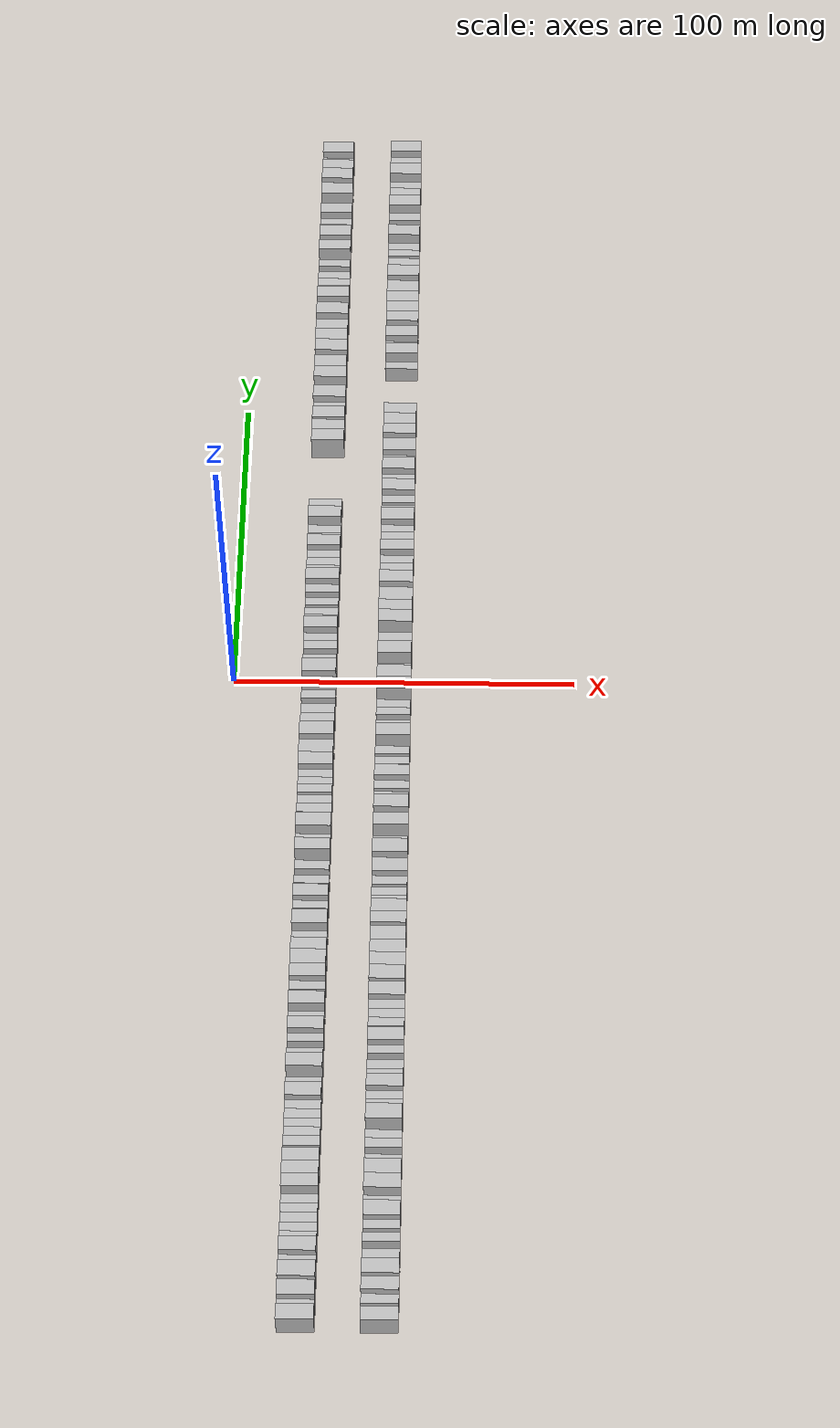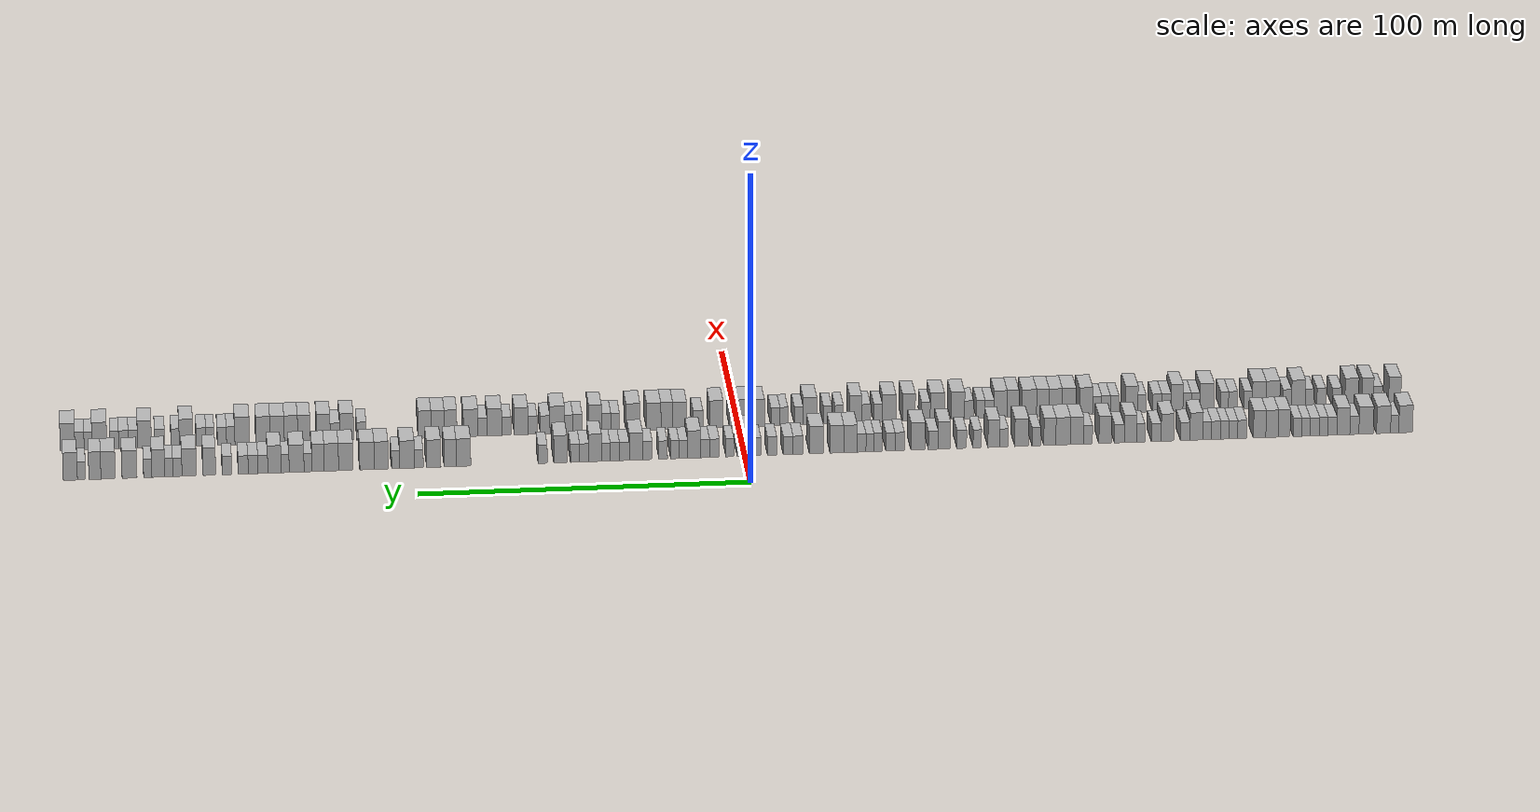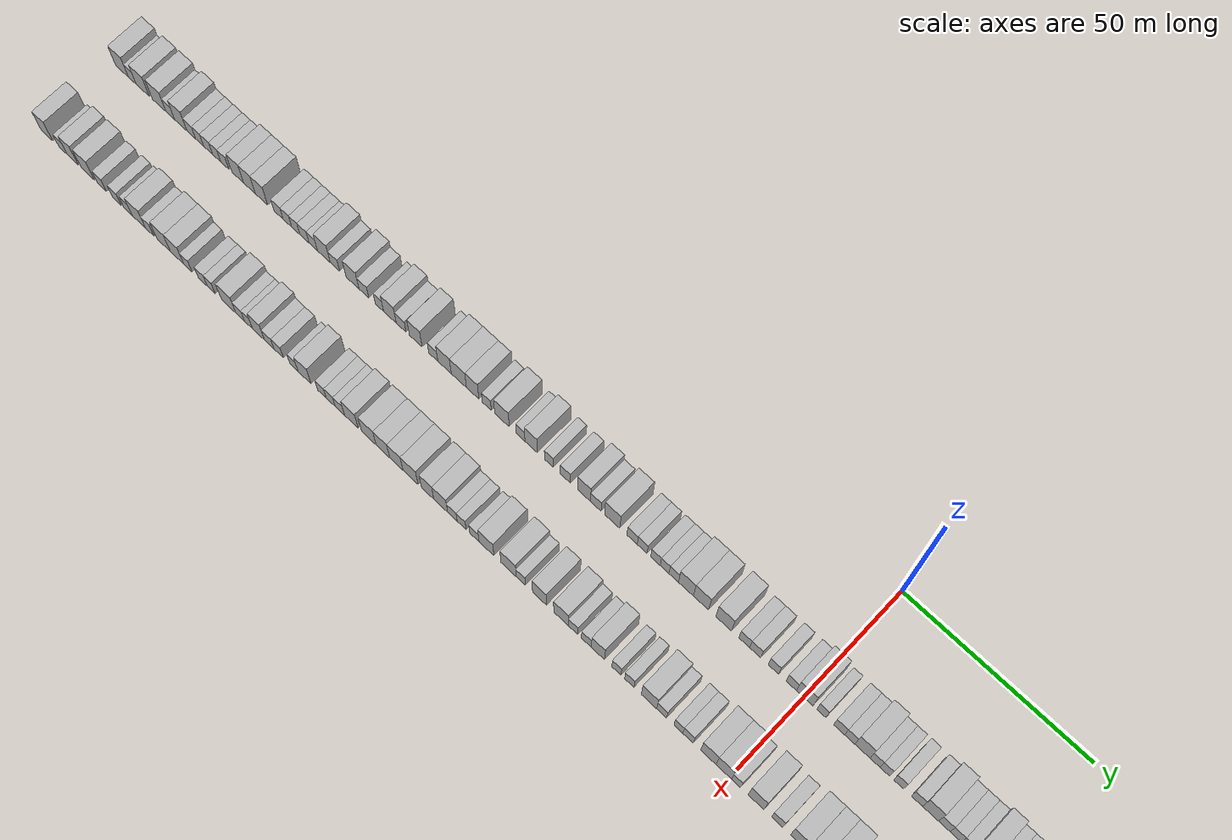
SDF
<sdf version="1.6">
 <world name="default">
  <scene>
   <sky><clouds><speed>12</speed></clouds></sky>
   <ambient>0.4 0.4 0.4 1</ambient>
   <background>0.7 0.7 0.7 1</background>
   <shadows>1</shadows>
  </scene>
  <gravity>0 0 -9.8066</gravity>
  <magnetic_field>6e-06 2.3e-05 -4.2e-05</magnetic_field>
  <physics default="0" name="default_physics" type="ode">
   <ode>
    <solver>
     <type>quick</type>
     <iters>10</iters>
     <sor>1.0</sor>
     <use_dynamic_moi_rescaling>0</use_dynamic_moi_rescaling>
    </solver>
    <constraints>
     <cfm>0</cfm>
     <erp>0.2</erp>
     <contact_max_correcting_vel>100</contact_max_correcting_vel>
     <contact_surface_layer>0.001</contact_surface_layer>
    </constraints>
   </ode>
   <max_step_size>0.004</max_step_size>
   <real_time_factor>1</real_time_factor>
   <real_time_update_rate>250</real_time_update_rate>
  </physics>
  <light name="sun" type="directional">
   <pose>0 0 10 0 0 0</pose>
   <diffuse>0.8 0.8 0.8 1</diffuse>
   <specular>0.2 0.2 0.2 1</specular>
   <attenuation>
    <range>1000</range>
    <constant>0.9</constant>
    <linear>0.01</linear>
    <quadratic>0.001</quadratic>
   </attenuation>
   <direction>-0.5 0.1 -0.9</direction>
  </light>
  <model name="building_1">
   <static>1</static>
   <pose>25.0000 -201.8803 0 0.000000 0.000000 0.000000</pose>
   <link name="link">
    <pose>0 0 4.50 0 0 0</pose>
    <collision name="collision"><geometry><box><size>10.0000 4.2395 9.0000</size></box></geometry></collision>
    <visual name="visual">
     <cast_shadows>0</cast_shadows>
     <geometry><box><size>10.0000 4.2395 9.0000</size></box></geometry>
     <material>
      <script>
       <uri>model://HANNAS_wall/materials/scripts</uri>
       <uri>model://HANNAS_wall/materials/textures</uri>
       <name>vrc/HANNAS_wall</name>
      </script>
     </material>
    </visual>
   </link>
  </model>
  <model name="building_2">
   <static>1</static>
   <pose>25.0000 -198.5039 0 0.000000 0.000000 0.000000</pose>
   <link name="link">
    <pose>0 0 3.00 0 0 0</pose>
    <collision name="collision"><geometry><box><size>10.0000 2.5133 6.0000</size></box></geometry></collision>
    <visual name="visual">
     <cast_shadows>0</cast_shadows>
     <geometry><box><size>10.0000 2.5133 6.0000</size></box></geometry>
     <material>
      <script>
       <uri>model://HANNAS_wall/materials/scripts</uri>
       <uri>model://HANNAS_wall/materials/textures</uri>
       <name>vrc/HANNAS_wall</name>
      </script>
     </material>
    </visual>
   </link>
  </model>
  <model name="building_3">
   <static>1</static>
   <pose>25.0000 -195.0967 0 0.000000 0.000000 0.000000</pose>
   <link name="link">
    <pose>0 0 4.50 0 0 0</pose>
    <collision name="collision"><geometry><box><size>10.0000 4.3011 9.0000</size></box></geometry></collision>
    <visual name="visual">
     <cast_shadows>0</cast_shadows>
     <geometry><box><size>10.0000 4.3011 9.0000</size></box></geometry>
     <material>
      <script>
       <uri>model://HANNAS_wall/materials/scripts</uri>
       <uri>model://HANNAS_wall/materials/textures</uri>
       <name>vrc/HANNAS_wall</name>
      </script>
     </material>
    </visual>
   </link>
  </model>
  <model name="building_4">
   <static>1</static>
   <pose>25.0000 -189.7284 0 0.000000 0.000000 0.000000</pose>
   <link name="link">
    <pose>0 0 4.50 0 0 0</pose>
    <collision name="collision"><geometry><box><size>10.0000 4.4355 9.0000</size></box></geometry></collision>
    <visual name="visual">
     <cast_shadows>0</cast_shadows>
     <geometry><box><size>10.0000 4.4355 9.0000</size></box></geometry>
     <material>
      <script>
       <uri>model://HANNAS_wall/materials/scripts</uri>
       <uri>model://HANNAS_wall/materials/textures</uri>
       <name>vrc/HANNAS_wall</name>
      </script>
     </material>
    </visual>
   </link>
  </model>
  <model name="building_5">
   <static>1</static>
   <pose>25.0000 -186.1232 0 0.000000 0.000000 0.000000</pose>
   <link name="link">
    <pose>0 0 3.00 0 0 0</pose>
    <collision name="collision"><geometry><box><size>10.0000 2.7748 6.0000</size></box></geometry></collision>
    <visual name="visual">
     <cast_shadows>0</cast_shadows>
     <geometry><box><size>10.0000 2.7748 6.0000</size></box></geometry>
     <material>
      <script>
       <uri>model://HANNAS_wall/materials/scripts</uri>
       <uri>model://HANNAS_wall/materials/textures</uri>
       <name>vrc/HANNAS_wall</name>
      </script>
     </material>
    </visual>
   </link>
  </model>
  <model name="building_6">
   <static>1</static>
   <pose>25.0000 -182.7527 0 0.000000 0.000000 0.000000</pose>
   <link name="link">
    <pose>0 0 4.50 0 0 0</pose>
    <collision name="collision"><geometry><box><size>10.0000 3.9661 9.0000</size></box></geometry></collision>
    <visual name="visual">
     <cast_shadows>0</cast_shadows>
     <geometry><box><size>10.0000 3.9661 9.0000</size></box></geometry>
     <material>
      <script>
       <uri>model://HANNAS_wall/materials/scripts</uri>
       <uri>model://HANNAS_wall/materials/textures</uri>
       <name>vrc/HANNAS_wall</name>
      </script>
     </material>
    </visual>
   </link>
  </model>
  <model name="building_7">
   <static>1</static>
   <pose>25.0000 -179.3696 0 0.000000 0.000000 0.000000</pose>
   <link name="link">
    <pose>0 0 3.00 0 0 0</pose>
    <collision name="collision"><geometry><box><size>10.0000 2.8002 6.0000</size></box></geometry></collision>
    <visual name="visual">
     <cast_shadows>0</cast_shadows>
     <geometry><box><size>10.0000 2.8002 6.0000</size></box></geometry>
     <material>
      <script>
       <uri>model://HANNAS_wall/materials/scripts</uri>
       <uri>model://HANNAS_wall/materials/textures</uri>
       <name>vrc/HANNAS_wall</name>
      </script>
     </material>
    </visual>
   </link>
  </model>
  <model name="building_8">
   <static>1</static>
   <pose>25.0000 -176.6806 0 0.000000 0.000000 0.000000</pose>
   <link name="link">
    <pose>0 0 3.00 0 0 0</pose>
    <collision name="collision"><geometry><box><size>10.0000 2.5779 6.0000</size></box></geometry></collision>
    <visual name="visual">
     <cast_shadows>0</cast_shadows>
     <geometry><box><size>10.0000 2.5779 6.0000</size></box></geometry>
     <material>
      <script>
       <uri>model://HANNAS_wall/materials/scripts</uri>
       <uri>model://HANNAS_wall/materials/textures</uri>
       <name>vrc/HANNAS_wall</name>
      </script>
     </material>
    </visual>
   </link>
  </model>
  <model name="building_9">
   <static>1</static>
   <pose>25.0000 -173.9446 0 0.000000 0.000000 0.000000</pose>
   <link name="link">
    <pose>0 0 3.00 0 0 0</pose>
    <collision name="collision"><geometry><box><size>10.0000 2.8940 6.0000</size></box></geometry></collision>
    <visual name="visual">
     <cast_shadows>0</cast_shadows>
     <geometry><box><size>10.0000 2.8940 6.0000</size></box></geometry>
     <material>
      <script>
       <uri>model://HANNAS_wall/materials/scripts</uri>
       <uri>model://HANNAS_wall/materials/textures</uri>
       <name>vrc/HANNAS_wall</name>
      </script>
     </material>
    </visual>
   </link>
  </model>
  <model name="building_10">
   <static>1</static>
   <pose>25.0000 -171.2128 0 0.000000 0.000000 0.000000</pose>
   <link name="link">
    <pose>0 0 3.00 0 0 0</pose>
    <collision name="collision"><geometry><box><size>10.0000 2.5696 6.0000</size></box></geometry></collision>
    <visual name="visual">
     <cast_shadows>0</cast_shadows>
     <geometry><box><size>10.0000 2.5696 6.0000</size></box></geometry>
     <material>
      <script>
       <uri>model://HANNAS_wall/materials/scripts</uri>
       <uri>model://HANNAS_wall/materials/textures</uri>
       <name>vrc/HANNAS_wall</name>
      </script>
     </material>
    </visual>
   </link>
  </model>
  <model name="building_11">
   <static>1</static>
   <pose>25.0000 -168.6348 0 0.000000 0.000000 0.000000</pose>
   <link name="link">
    <pose>0 0 3.00 0 0 0</pose>
    <collision name="collision"><geometry><box><size>10.0000 2.5864 6.0000</size></box></geometry></collision>
    <visual name="visual">
     <cast_shadows>0</cast_shadows>
     <geometry><box><size>10.0000 2.5864 6.0000</size></box></geometry>
     <material>
      <script>
       <uri>model://HANNAS_wall/materials/scripts</uri>
       <uri>model://HANNAS_wall/materials/textures</uri>
       <name>vrc/HANNAS_wall</name>
      </script>
     </material>
    </visual>
   </link>
  </model>
  <model name="building_12">
   <static>1</static>
   <pose>25.0000 -164.5140 0 0.000000 0.000000 0.000000</pose>
   <link name="link">
    <pose>0 0 4.50 0 0 0</pose>
    <collision name="collision"><geometry><box><size>10.0000 3.6553 9.0000</size></box></geometry></collision>
    <visual name="visual">
     <cast_shadows>0</cast_shadows>
     <geometry><box><size>10.0000 3.6553 9.0000</size></box></geometry>
     <material>
      <script>
       <uri>model://HANNAS_wall/materials/scripts</uri>
       <uri>model://HANNAS_wall/materials/textures</uri>
       <name>vrc/HANNAS_wall</name>
      </script>
     </material>
    </visual>
   </link>
  </model>
  <model name="building_13">
   <static>1</static>
   <pose>25.0000 -160.7998 0 0.000000 0.000000 0.000000</pose>
   <link name="link">
    <pose>0 0 4.50 0 0 0</pose>
    <collision name="collision"><geometry><box><size>10.0000 3.7731 9.0000</size></box></geometry></collision>
    <visual name="visual">
     <cast_shadows>0</cast_shadows>
     <geometry><box><size>10.0000 3.7731 9.0000</size></box></geometry>
     <material>
      <script>
       <uri>model://HANNAS_wall/materials/scripts</uri>
       <uri>model://HANNAS_wall/materials/textures</uri>
       <name>vrc/HANNAS_wall</name>
      </script>
     </material>
    </visual>
   </link>
  </model>
  <model name="building_14">
   <static>1</static>
   <pose>25.0000 -157.0028 0 0.000000 0.000000 0.000000</pose>
   <link name="link">
    <pose>0 0 4.50 0 0 0</pose>
    <collision name="collision"><geometry><box><size>10.0000 3.8210 9.0000</size></box></geometry></collision>
    <visual name="visual">
     <cast_shadows>0</cast_shadows>
     <geometry><box><size>10.0000 3.8210 9.0000</size></box></geometry>
     <material>
      <script>
       <uri>model://HANNAS_wall/materials/scripts</uri>
       <uri>model://HANNAS_wall/materials/textures</uri>
       <name>vrc/HANNAS_wall</name>
      </script>
     </material>
    </visual>
   </link>
  </model>
  <model name="building_15">
   <static>1</static>
   <pose>25.0000 -151.6725 0 0.000000 0.000000 0.000000</pose>
   <link name="link">
    <pose>0 0 3.00 0 0 0</pose>
    <collision name="collision"><geometry><box><size>10.0000 2.8395 6.0000</size></box></geometry></collision>
    <visual name="visual">
     <cast_shadows>0</cast_shadows>
     <geometry><box><size>10.0000 2.8395 6.0000</size></box></geometry>
     <material>
      <script>
       <uri>model://HANNAS_wall/materials/scripts</uri>
       <uri>model://HANNAS_wall/materials/textures</uri>
       <name>vrc/HANNAS_wall</name>
      </script>
     </material>
    </visual>
   </link>
  </model>
  <model name="building_16">
   <static>1</static>
   <pose>25.0000 -148.9115 0 0.000000 0.000000 0.000000</pose>
   <link name="link">
    <pose>0 0 3.00 0 0 0</pose>
    <collision name="collision"><geometry><box><size>10.0000 2.6826 6.0000</size></box></geometry></collision>
    <visual name="visual">
     <cast_shadows>0</cast_shadows>
     <geometry><box><size>10.0000 2.6826 6.0000</size></box></geometry>
     <material>
      <script>
       <uri>model://HANNAS_wall/materials/scripts</uri>
       <uri>model://HANNAS_wall/materials/textures</uri>
       <name>vrc/HANNAS_wall</name>
      </script>
     </material>
    </visual>
   </link>
  </model>
  <model name="building_17">
   <static>1</static>
   <pose>25.0000 -146.3011 0 0.000000 0.000000 0.000000</pose>
   <link name="link">
    <pose>0 0 3.00 0 0 0</pose>
    <collision name="collision"><geometry><box><size>10.0000 2.5381 6.0000</size></box></geometry></collision>
    <visual name="visual">
     <cast_shadows>0</cast_shadows>
     <geometry><box><size>10.0000 2.5381 6.0000</size></box></geometry>
     <material>
      <script>
       <uri>model://HANNAS_wall/materials/scripts</uri>
       <uri>model://HANNAS_wall/materials/textures</uri>
       <name>vrc/HANNAS_wall</name>
      </script>
     </material>
    </visual>
   </link>
  </model>
  <model name="building_18">
   <static>1</static>
   <pose>25.0000 -143.6100 0 0.000000 0.000000 0.000000</pose>
   <link name="link">
    <pose>0 0 3.00 0 0 0</pose>
    <collision name="collision"><geometry><box><size>10.0000 2.8442 6.0000</size></box></geometry></collision>
    <visual name="visual">
     <cast_shadows>0</cast_shadows>
     <geometry><box><size>10.0000 2.8442 6.0000</size></box></geometry>
     <material>
      <script>
       <uri>model://HANNAS_wall/materials/scripts</uri>
       <uri>model://HANNAS_wall/materials/textures</uri>
       <name>vrc/HANNAS_wall</name>
      </script>
     </material>
    </visual>
   </link>
  </model>
  <model name="building_19">
   <static>1</static>
   <pose>25.0000 -140.8965 0 0.000000 0.000000 0.000000</pose>
   <link name="link">
    <pose>0 0 3.00 0 0 0</pose>
    <collision name="collision"><geometry><box><size>10.0000 2.5828 6.0000</size></box></geometry></collision>
    <visual name="visual">
     <cast_shadows>0</cast_shadows>
     <geometry><box><size>10.0000 2.5828 6.0000</size></box></geometry>
     <material>
      <script>
       <uri>model://HANNAS_wall/materials/scripts</uri>
       <uri>model://HANNAS_wall/materials/textures</uri>
       <name>vrc/HANNAS_wall</name>
      </script>
     </material>
    </visual>
   </link>
  </model>
  <model name="building_20">
   <static>1</static>
   <pose>25.0000 -137.6247 0 0.000000 0.000000 0.000000</pose>
   <link name="link">
    <pose>0 0 4.50 0 0 0</pose>
    <collision name="collision"><geometry><box><size>10.0000 3.9608 9.0000</size></box></geometry></collision>
    <visual name="visual">
     <cast_shadows>0</cast_shadows>
     <geometry><box><size>10.0000 3.9608 9.0000</size></box></geometry>
     <material>
      <script>
       <uri>model://HANNAS_wall/materials/scripts</uri>
       <uri>model://HANNAS_wall/materials/textures</uri>
       <name>vrc/HANNAS_wall</name>
      </script>
     </material>
    </visual>
   </link>
  </model>
  <model name="building_21">
   <static>1</static>
   <pose>25.0000 -134.1965 0 0.000000 0.000000 0.000000</pose>
   <link name="link">
    <pose>0 0 3.00 0 0 0</pose>
    <collision name="collision"><geometry><box><size>10.0000 2.8956 6.0000</size></box></geometry></collision>
    <visual name="visual">
     <cast_shadows>0</cast_shadows>
     <geometry><box><size>10.0000 2.8956 6.0000</size></box></geometry>
     <material>
      <script>
       <uri>model://HANNAS_wall/materials/scripts</uri>
       <uri>model://HANNAS_wall/materials/textures</uri>
       <name>vrc/HANNAS_wall</name>
      </script>
     </material>
    </visual>
   </link>
  </model>
  <model name="building_22">
   <static>1</static>
   <pose>25.0000 -128.7804 0 0.000000 0.000000 0.000000</pose>
   <link name="link">
    <pose>0 0 4.50 0 0 0</pose>
    <collision name="collision"><geometry><box><size>10.0000 3.9366 9.0000</size></box></geometry></collision>
    <visual name="visual">
     <cast_shadows>0</cast_shadows>
     <geometry><box><size>10.0000 3.9366 9.0000</size></box></geometry>
     <material>
      <script>
       <uri>model://HANNAS_wall/materials/scripts</uri>
       <uri>model://HANNAS_wall/materials/textures</uri>
       <name>vrc/HANNAS_wall</name>
      </script>
     </material>
    </visual>
   </link>
  </model>
  <model name="building_23">
   <static>1</static>
   <pose>25.0000 -125.3227 0 0.000000 0.000000 0.000000</pose>
   <link name="link">
    <pose>0 0 3.00 0 0 0</pose>
    <collision name="collision"><geometry><box><size>10.0000 2.9788 6.0000</size></box></geometry></collision>
    <visual name="visual">
     <cast_shadows>0</cast_shadows>
     <geometry><box><size>10.0000 2.9788 6.0000</size></box></geometry>
     <material>
      <script>
       <uri>model://HANNAS_wall/materials/scripts</uri>
       <uri>model://HANNAS_wall/materials/textures</uri>
       <name>vrc/HANNAS_wall</name>
      </script>
     </material>
    </visual>
   </link>
  </model>
  <model name="building_24">
   <static>1</static>
   <pose>25.0000 -120.5903 0 0.000000 0.000000 0.000000</pose>
   <link name="link">
    <pose>0 0 3.00 0 0 0</pose>
    <collision name="collision"><geometry><box><size>10.0000 2.4859 6.0000</size></box></geometry></collision>
    <visual name="visual">
     <cast_shadows>0</cast_shadows>
     <geometry><box><size>10.0000 2.4859 6.0000</size></box></geometry>
     <material>
      <script>
       <uri>model://HANNAS_wall/materials/scripts</uri>
       <uri>model://HANNAS_wall/materials/textures</uri>
       <name>vrc/HANNAS_wall</name>
      </script>
     </material>
    </visual>
   </link>
  </model>
  <model name="building_25">
   <static>1</static>
   <pose>25.0000 -117.4405 0 0.000000 0.000000 0.000000</pose>
   <link name="link">
    <pose>0 0 4.50 0 0 0</pose>
    <collision name="collision"><geometry><box><size>10.0000 3.8137 9.0000</size></box></geometry></collision>
    <visual name="visual">
     <cast_shadows>0</cast_shadows>
     <geometry><box><size>10.0000 3.8137 9.0000</size></box></geometry>
     <material>
      <script>
       <uri>model://HANNAS_wall/materials/scripts</uri>
       <uri>model://HANNAS_wall/materials/textures</uri>
       <name>vrc/HANNAS_wall</name>
      </script>
     </material>
    </visual>
   </link>
  </model>
  <model name="building_26">
   <static>1</static>
   <pose>25.0000 -114.0480 0 0.000000 0.000000 0.000000</pose>
   <link name="link">
    <pose>0 0 3.00 0 0 0</pose>
    <collision name="collision"><geometry><box><size>10.0000 2.9712 6.0000</size></box></geometry></collision>
    <visual name="visual">
     <cast_shadows>0</cast_shadows>
     <geometry><box><size>10.0000 2.9712 6.0000</size></box></geometry>
     <material>
      <script>
       <uri>model://HANNAS_wall/materials/scripts</uri>
       <uri>model://HANNAS_wall/materials/textures</uri>
       <name>vrc/HANNAS_wall</name>
      </script>
     </material>
    </visual>
   </link>
  </model>
  <model name="building_27">
   <static>1</static>
   <pose>25.0000 -109.6713 0 0.000000 0.000000 0.000000</pose>
   <link name="link">
    <pose>0 0 4.50 0 0 0</pose>
    <collision name="collision"><geometry><box><size>10.0000 3.7821 9.0000</size></box></geometry></collision>
    <visual name="visual">
     <cast_shadows>0</cast_shadows>
     <geometry><box><size>10.0000 3.7821 9.0000</size></box></geometry>
     <material>
      <script>
       <uri>model://HANNAS_wall/materials/scripts</uri>
       <uri>model://HANNAS_wall/materials/textures</uri>
       <name>vrc/HANNAS_wall</name>
      </script>
     </material>
    </visual>
   </link>
  </model>
  <model name="building_28">
   <static>1</static>
   <pose>25.0000 -104.4233 0 0.000000 0.000000 0.000000</pose>
   <link name="link">
    <pose>0 0 3.00 0 0 0</pose>
    <collision name="collision"><geometry><box><size>10.0000 2.7140 6.0000</size></box></geometry></collision>
    <visual name="visual">
     <cast_shadows>0</cast_shadows>
     <geometry><box><size>10.0000 2.7140 6.0000</size></box></geometry>
     <material>
      <script>
       <uri>model://HANNAS_wall/materials/scripts</uri>
       <uri>model://HANNAS_wall/materials/textures</uri>
       <name>vrc/HANNAS_wall</name>
      </script>
     </material>
    </visual>
   </link>
  </model>
  <model name="building_29">
   <static>1</static>
   <pose>25.0000 -101.0725 0 0.000000 0.000000 0.000000</pose>
   <link name="link">
    <pose>0 0 4.50 0 0 0</pose>
    <collision name="collision"><geometry><box><size>10.0000 3.9875 9.0000</size></box></geometry></collision>
    <visual name="visual">
     <cast_shadows>0</cast_shadows>
     <geometry><box><size>10.0000 3.9875 9.0000</size></box></geometry>
     <material>
      <script>
       <uri>model://HANNAS_wall/materials/scripts</uri>
       <uri>model://HANNAS_wall/materials/textures</uri>
       <name>vrc/HANNAS_wall</name>
      </script>
     </material>
    </visual>
   </link>
  </model>
  <model name="building_30">
   <static>1</static>
   <pose>25.0000 -96.8484 0 0.000000 0.000000 0.000000</pose>
   <link name="link">
    <pose>0 0 4.50 0 0 0</pose>
    <collision name="collision"><geometry><box><size>10.0000 4.4606 9.0000</size></box></geometry></collision>
    <visual name="visual">
     <cast_shadows>0</cast_shadows>
     <geometry><box><size>10.0000 4.4606 9.0000</size></box></geometry>
     <material>
      <script>
       <uri>model://HANNAS_wall/materials/scripts</uri>
       <uri>model://HANNAS_wall/materials/textures</uri>
       <name>vrc/HANNAS_wall</name>
      </script>
     </material>
    </visual>
   </link>
  </model>
  <model name="building_31">
   <static>1</static>
   <pose>25.0000 -92.7761 0 0.000000 0.000000 0.000000</pose>
   <link name="link">
    <pose>0 0 4.50 0 0 0</pose>
    <collision name="collision"><geometry><box><size>10.0000 3.6841 9.0000</size></box></geometry></collision>
    <visual name="visual">
     <cast_shadows>0</cast_shadows>
     <geometry><box><size>10.0000 3.6841 9.0000</size></box></geometry>
     <material>
      <script>
       <uri>model://HANNAS_wall/materials/scripts</uri>
       <uri>model://HANNAS_wall/materials/textures</uri>
       <name>vrc/HANNAS_wall</name>
      </script>
     </material>
    </visual>
   </link>
  </model>
  <model name="building_32">
   <static>1</static>
   <pose>25.0000 -88.6249 0 0.000000 0.000000 0.000000</pose>
   <link name="link">
    <pose>0 0 3.00 0 0 0</pose>
    <collision name="collision"><geometry><box><size>10.0000 2.6183 6.0000</size></box></geometry></collision>
    <visual name="visual">
     <cast_shadows>0</cast_shadows>
     <geometry><box><size>10.0000 2.6183 6.0000</size></box></geometry>
     <material>
      <script>
       <uri>model://HANNAS_wall/materials/scripts</uri>
       <uri>model://HANNAS_wall/materials/textures</uri>
       <name>vrc/HANNAS_wall</name>
      </script>
     </material>
    </visual>
   </link>
  </model>
  <model name="building_33">
   <static>1</static>
   <pose>25.0000 -84.1977 0 0.000000 0.000000 0.000000</pose>
   <link name="link">
    <pose>0 0 4.50 0 0 0</pose>
    <collision name="collision"><geometry><box><size>10.0000 4.2360 9.0000</size></box></geometry></collision>
    <visual name="visual">
     <cast_shadows>0</cast_shadows>
     <geometry><box><size>10.0000 4.2360 9.0000</size></box></geometry>
     <material>
      <script>
       <uri>model://HANNAS_wall/materials/scripts</uri>
       <uri>model://HANNAS_wall/materials/textures</uri>
       <name>vrc/HANNAS_wall</name>
      </script>
     </material>
    </visual>
   </link>
  </model>
  <model name="building_34">
   <static>1</static>
   <pose>25.0000 -78.7950 0 0.000000 0.000000 0.000000</pose>
   <link name="link">
    <pose>0 0 3.00 0 0 0</pose>
    <collision name="collision"><geometry><box><size>10.0000 2.5693 6.0000</size></box></geometry></collision>
    <visual name="visual">
     <cast_shadows>0</cast_shadows>
     <geometry><box><size>10.0000 2.5693 6.0000</size></box></geometry>
     <material>
      <script>
       <uri>model://HANNAS_wall/materials/scripts</uri>
       <uri>model://HANNAS_wall/materials/textures</uri>
       <name>vrc/HANNAS_wall</name>
      </script>
     </material>
    </visual>
   </link>
  </model>
  <model name="building_35">
   <static>1</static>
   <pose>25.0000 -75.6955 0 0.000000 0.000000 0.000000</pose>
   <link name="link">
    <pose>0 0 4.50 0 0 0</pose>
    <collision name="collision"><geometry><box><size>10.0000 3.6298 9.0000</size></box></geometry></collision>
    <visual name="visual">
     <cast_shadows>0</cast_shadows>
     <geometry><box><size>10.0000 3.6298 9.0000</size></box></geometry>
     <material>
      <script>
       <uri>model://HANNAS_wall/materials/scripts</uri>
       <uri>model://HANNAS_wall/materials/textures</uri>
       <name>vrc/HANNAS_wall</name>
      </script>
     </material>
    </visual>
   </link>
  </model>
  <model name="building_36">
   <static>1</static>
   <pose>25.0000 -70.6158 0 0.000000 0.000000 0.000000</pose>
   <link name="link">
    <pose>0 0 3.00 0 0 0</pose>
    <collision name="collision"><geometry><box><size>10.0000 2.5295 6.0000</size></box></geometry></collision>
    <visual name="visual">
     <cast_shadows>0</cast_shadows>
     <geometry><box><size>10.0000 2.5295 6.0000</size></box></geometry>
     <material>
      <script>
       <uri>model://HANNAS_wall/materials/scripts</uri>
       <uri>model://HANNAS_wall/materials/textures</uri>
       <name>vrc/HANNAS_wall</name>
      </script>
     </material>
    </visual>
   </link>
  </model>
  <model name="building_37">
   <static>1</static>
   <pose>25.0000 -65.8917 0 0.000000 0.000000 0.000000</pose>
   <link name="link">
    <pose>0 0 3.00 0 0 0</pose>
    <collision name="collision"><geometry><box><size>10.0000 2.9186 6.0000</size></box></geometry></collision>
    <visual name="visual">
     <cast_shadows>0</cast_shadows>
     <geometry><box><size>10.0000 2.9186 6.0000</size></box></geometry>
     <material>
      <script>
       <uri>model://HANNAS_wall/materials/scripts</uri>
       <uri>model://HANNAS_wall/materials/textures</uri>
       <name>vrc/HANNAS_wall</name>
      </script>
     </material>
    </visual>
   </link>
  </model>
  <model name="building_38">
   <static>1</static>
   <pose>25.0000 -60.5771 0 0.000000 0.000000 0.000000</pose>
   <link name="link">
    <pose>0 0 4.50 0 0 0</pose>
    <collision name="collision"><geometry><box><size>10.0000 3.7107 9.0000</size></box></geometry></collision>
    <visual name="visual">
     <cast_shadows>0</cast_shadows>
     <geometry><box><size>10.0000 3.7107 9.0000</size></box></geometry>
     <material>
      <script>
       <uri>model://HANNAS_wall/materials/scripts</uri>
       <uri>model://HANNAS_wall/materials/textures</uri>
       <name>vrc/HANNAS_wall</name>
      </script>
     </material>
    </visual>
   </link>
  </model>
  <model name="building_39">
   <static>1</static>
   <pose>25.0000 -57.2219 0 0.000000 0.000000 0.000000</pose>
   <link name="link">
    <pose>0 0 3.00 0 0 0</pose>
    <collision name="collision"><geometry><box><size>10.0000 2.9997 6.0000</size></box></geometry></collision>
    <visual name="visual">
     <cast_shadows>0</cast_shadows>
     <geometry><box><size>10.0000 2.9997 6.0000</size></box></geometry>
     <material>
      <script>
       <uri>model://HANNAS_wall/materials/scripts</uri>
       <uri>model://HANNAS_wall/materials/textures</uri>
       <name>vrc/HANNAS_wall</name>
      </script>
     </material>
    </visual>
   </link>
  </model>
  <model name="building_40">
   <static>1</static>
   <pose>25.0000 -52.5726 0 0.000000 0.000000 0.000000</pose>
   <link name="link">
    <pose>0 0 4.50 0 0 0</pose>
    <collision name="collision"><geometry><box><size>10.0000 4.2988 9.0000</size></box></geometry></collision>
    <visual name="visual">
     <cast_shadows>0</cast_shadows>
     <geometry><box><size>10.0000 4.2988 9.0000</size></box></geometry>
     <material>
      <script>
       <uri>model://HANNAS_wall/materials/scripts</uri>
       <uri>model://HANNAS_wall/materials/textures</uri>
       <name>vrc/HANNAS_wall</name>
      </script>
     </material>
    </visual>
   </link>
  </model>
  <model name="building_41">
   <static>1</static>
   <pose>25.0000 -46.9709 0 0.000000 0.000000 0.000000</pose>
   <link name="link">
    <pose>0 0 3.00 0 0 0</pose>
    <collision name="collision"><geometry><box><size>10.0000 2.9047 6.0000</size></box></geometry></collision>
    <visual name="visual">
     <cast_shadows>0</cast_shadows>
     <geometry><box><size>10.0000 2.9047 6.0000</size></box></geometry>
     <material>
      <script>
       <uri>model://HANNAS_wall/materials/scripts</uri>
       <uri>model://HANNAS_wall/materials/textures</uri>
       <name>vrc/HANNAS_wall</name>
      </script>
     </material>
    </visual>
   </link>
  </model>
  <model name="building_42">
   <static>1</static>
   <pose>25.0000 -44.1402 0 0.000000 0.000000 0.000000</pose>
   <link name="link">
    <pose>0 0 3.00 0 0 0</pose>
    <collision name="collision"><geometry><box><size>10.0000 2.7567 6.0000</size></box></geometry></collision>
    <visual name="visual">
     <cast_shadows>0</cast_shadows>
     <geometry><box><size>10.0000 2.7567 6.0000</size></box></geometry>
     <material>
      <script>
       <uri>model://HANNAS_wall/materials/scripts</uri>
       <uri>model://HANNAS_wall/materials/textures</uri>
       <name>vrc/HANNAS_wall</name>
      </script>
     </material>
    </visual>
   </link>
  </model>
  <model name="building_43">
   <static>1</static>
   <pose>25.0000 -40.4365 0 0.000000 0.000000 0.000000</pose>
   <link name="link">
    <pose>0 0 3.00 0 0 0</pose>
    <collision name="collision"><geometry><box><size>10.0000 2.6507 6.0000</size></box></geometry></collision>
    <visual name="visual">
     <cast_shadows>0</cast_shadows>
     <geometry><box><size>10.0000 2.6507 6.0000</size></box></geometry>
     <material>
      <script>
       <uri>model://HANNAS_wall/materials/scripts</uri>
       <uri>model://HANNAS_wall/materials/textures</uri>
       <name>vrc/HANNAS_wall</name>
      </script>
     </material>
    </visual>
   </link>
  </model>
  <model name="building_44">
   <static>1</static>
   <pose>25.0000 -37.9015 0 0.000000 0.000000 0.000000</pose>
   <link name="link">
    <pose>0 0 3.00 0 0 0</pose>
    <collision name="collision"><geometry><box><size>10.0000 2.4193 6.0000</size></box></geometry></collision>
    <visual name="visual">
     <cast_shadows>0</cast_shadows>
     <geometry><box><size>10.0000 2.4193 6.0000</size></box></geometry>
     <material>
      <script>
       <uri>model://HANNAS_wall/materials/scripts</uri>
       <uri>model://HANNAS_wall/materials/textures</uri>
       <name>vrc/HANNAS_wall</name>
      </script>
     </material>
    </visual>
   </link>
  </model>
  <model name="building_45">
   <static>1</static>
   <pose>25.0000 -35.3691 0 0.000000 0.000000 0.000000</pose>
   <link name="link">
    <pose>0 0 3.00 0 0 0</pose>
    <collision name="collision"><geometry><box><size>10.0000 2.6455 6.0000</size></box></geometry></collision>
    <visual name="visual">
     <cast_shadows>0</cast_shadows>
     <geometry><box><size>10.0000 2.6455 6.0000</size></box></geometry>
     <material>
      <script>
       <uri>model://HANNAS_wall/materials/scripts</uri>
       <uri>model://HANNAS_wall/materials/textures</uri>
       <name>vrc/HANNAS_wall</name>
      </script>
     </material>
    </visual>
   </link>
  </model>
  <model name="building_46">
   <static>1</static>
   <pose>25.0000 -31.9945 0 0.000000 0.000000 0.000000</pose>
   <link name="link">
    <pose>0 0 4.50 0 0 0</pose>
    <collision name="collision"><geometry><box><size>10.0000 4.1037 9.0000</size></box></geometry></collision>
    <visual name="visual">
     <cast_shadows>0</cast_shadows>
     <geometry><box><size>10.0000 4.1037 9.0000</size></box></geometry>
     <material>
      <script>
       <uri>model://HANNAS_wall/materials/scripts</uri>
       <uri>model://HANNAS_wall/materials/textures</uri>
       <name>vrc/HANNAS_wall</name>
      </script>
     </material>
    </visual>
   </link>
  </model>
  <model name="building_47">
   <static>1</static>
   <pose>25.0000 -27.8611 0 0.000000 0.000000 0.000000</pose>
   <link name="link">
    <pose>0 0 4.50 0 0 0</pose>
    <collision name="collision"><geometry><box><size>10.0000 4.1633 9.0000</size></box></geometry></collision>
    <visual name="visual">
     <cast_shadows>0</cast_shadows>
     <geometry><box><size>10.0000 4.1633 9.0000</size></box></geometry>
     <material>
      <script>
       <uri>model://HANNAS_wall/materials/scripts</uri>
       <uri>model://HANNAS_wall/materials/textures</uri>
       <name>vrc/HANNAS_wall</name>
      </script>
     </material>
    </visual>
   </link>
  </model>
  <model name="building_48">
   <static>1</static>
   <pose>25.0000 -21.6405 0 0.000000 0.000000 0.000000</pose>
   <link name="link">
    <pose>0 0 4.50 0 0 0</pose>
    <collision name="collision"><geometry><box><size>10.0000 4.2778 9.0000</size></box></geometry></collision>
    <visual name="visual">
     <cast_shadows>0</cast_shadows>
     <geometry><box><size>10.0000 4.2778 9.0000</size></box></geometry>
     <material>
      <script>
       <uri>model://HANNAS_wall/materials/scripts</uri>
       <uri>model://HANNAS_wall/materials/textures</uri>
       <name>vrc/HANNAS_wall</name>
      </script>
     </material>
    </visual>
   </link>
  </model>
  <model name="building_49">
   <static>1</static>
   <pose>25.0000 -16.0252 0 0.000000 0.000000 0.000000</pose>
   <link name="link">
    <pose>0 0 3.00 0 0 0</pose>
    <collision name="collision"><geometry><box><size>10.0000 2.9528 6.0000</size></box></geometry></collision>
    <visual name="visual">
     <cast_shadows>0</cast_shadows>
     <geometry><box><size>10.0000 2.9528 6.0000</size></box></geometry>
     <material>
      <script>
       <uri>model://HANNAS_wall/materials/scripts</uri>
       <uri>model://HANNAS_wall/materials/textures</uri>
       <name>vrc/HANNAS_wall</name>
      </script>
     </material>
    </visual>
   </link>
  </model>
  <model name="building_50">
   <static>1</static>
   <pose>25.0000 -13.0524 0 0.000000 0.000000 0.000000</pose>
   <link name="link">
    <pose>0 0 3.00 0 0 0</pose>
    <collision name="collision"><geometry><box><size>10.0000 2.9929 6.0000</size></box></geometry></collision>
    <visual name="visual">
     <cast_shadows>0</cast_shadows>
     <geometry><box><size>10.0000 2.9929 6.0000</size></box></geometry>
     <material>
      <script>
       <uri>model://HANNAS_wall/materials/scripts</uri>
       <uri>model://HANNAS_wall/materials/textures</uri>
       <name>vrc/HANNAS_wall</name>
      </script>
     </material>
    </visual>
   </link>
  </model>
  <model name="building_51">
   <static>1</static>
   <pose>25.0000 -8.1540 0 0.000000 0.000000 0.000000</pose>
   <link name="link">
    <pose>0 0 3.00 0 0 0</pose>
    <collision name="collision"><geometry><box><size>10.0000 2.8040 6.0000</size></box></geometry></collision>
    <visual name="visual">
     <cast_shadows>0</cast_shadows>
     <geometry><box><size>10.0000 2.8040 6.0000</size></box></geometry>
     <material>
      <script>
       <uri>model://HANNAS_wall/materials/scripts</uri>
       <uri>model://HANNAS_wall/materials/textures</uri>
       <name>vrc/HANNAS_wall</name>
      </script>
     </material>
    </visual>
   </link>
  </model>
  <model name="building_52">
   <static>1</static>
   <pose>25.0000 -3.3668 0 0.000000 0.000000 0.000000</pose>
   <link name="link">
    <pose>0 0 3.00 0 0 0</pose>
    <collision name="collision"><geometry><box><size>10.0000 2.7705 6.0000</size></box></geometry></collision>
    <visual name="visual">
     <cast_shadows>0</cast_shadows>
     <geometry><box><size>10.0000 2.7705 6.0000</size></box></geometry>
     <material>
      <script>
       <uri>model://HANNAS_wall/materials/scripts</uri>
       <uri>model://HANNAS_wall/materials/textures</uri>
       <name>vrc/HANNAS_wall</name>
      </script>
     </material>
    </visual>
   </link>
  </model>
  <model name="building_53">
   <static>1</static>
   <pose>25.0000 0.2383 0 0.000000 0.000000 0.000000</pose>
   <link name="link">
    <pose>0 0 4.50 0 0 0</pose>
    <collision name="collision"><geometry><box><size>10.0000 4.4397 9.0000</size></box></geometry></collision>
    <visual name="visual">
     <cast_shadows>0</cast_shadows>
     <geometry><box><size>10.0000 4.4397 9.0000</size></box></geometry>
     <material>
      <script>
       <uri>model://HANNAS_wall/materials/scripts</uri>
       <uri>model://HANNAS_wall/materials/textures</uri>
       <name>vrc/HANNAS_wall</name>
      </script>
     </material>
    </visual>
   </link>
  </model>
  <model name="building_54">
   <static>1</static>
   <pose>25.0000 4.6681 0 0.000000 0.000000 0.000000</pose>
   <link name="link">
    <pose>0 0 3.00 0 0 0</pose>
    <collision name="collision"><geometry><box><size>10.0000 2.4198 6.0000</size></box></geometry></collision>
    <visual name="visual">
     <cast_shadows>0</cast_shadows>
     <geometry><box><size>10.0000 2.4198 6.0000</size></box></geometry>
     <material>
      <script>
       <uri>model://HANNAS_wall/materials/scripts</uri>
       <uri>model://HANNAS_wall/materials/textures</uri>
       <name>vrc/HANNAS_wall</name>
      </script>
     </material>
    </visual>
   </link>
  </model>
  <model name="building_55">
   <static>1</static>
   <pose>25.0000 9.3480 0 0.000000 0.000000 0.000000</pose>
   <link name="link">
    <pose>0 0 3.00 0 0 0</pose>
    <collision name="collision"><geometry><box><size>10.0000 2.9400 6.0000</size></box></geometry></collision>
    <visual name="visual">
     <cast_shadows>0</cast_shadows>
     <geometry><box><size>10.0000 2.9400 6.0000</size></box></geometry>
     <material>
      <script>
       <uri>model://HANNAS_wall/materials/scripts</uri>
       <uri>model://HANNAS_wall/materials/textures</uri>
       <name>vrc/HANNAS_wall</name>
      </script>
     </material>
    </visual>
   </link>
  </model>
  <model name="building_56">
   <static>1</static>
   <pose>25.0000 12.1555 0 0.000000 0.000000 0.000000</pose>
   <link name="link">
    <pose>0 0 3.00 0 0 0</pose>
    <collision name="collision"><geometry><box><size>10.0000 2.6751 6.0000</size></box></geometry></collision>
    <visual name="visual">
     <cast_shadows>0</cast_shadows>
     <geometry><box><size>10.0000 2.6751 6.0000</size></box></geometry>
     <material>
      <script>
       <uri>model://HANNAS_wall/materials/scripts</uri>
       <uri>model://HANNAS_wall/materials/textures</uri>
       <name>vrc/HANNAS_wall</name>
      </script>
     </material>
    </visual>
   </link>
  </model>
  <model name="building_57">
   <static>1</static>
   <pose>25.0000 15.4903 0 0.000000 0.000000 0.000000</pose>
   <link name="link">
    <pose>0 0 4.50 0 0 0</pose>
    <collision name="collision"><geometry><box><size>10.0000 3.9945 9.0000</size></box></geometry></collision>
    <visual name="visual">
     <cast_shadows>0</cast_shadows>
     <geometry><box><size>10.0000 3.9945 9.0000</size></box></geometry>
     <material>
      <script>
       <uri>model://HANNAS_wall/materials/scripts</uri>
       <uri>model://HANNAS_wall/materials/textures</uri>
       <name>vrc/HANNAS_wall</name>
      </script>
     </material>
    </visual>
   </link>
  </model>
  <model name="building_58">
   <static>1</static>
   <pose>25.0000 18.8014 0 0.000000 0.000000 0.000000</pose>
   <link name="link">
    <pose>0 0 3.00 0 0 0</pose>
    <collision name="collision"><geometry><box><size>10.0000 2.6277 6.0000</size></box></geometry></collision>
    <visual name="visual">
     <cast_shadows>0</cast_shadows>
     <geometry><box><size>10.0000 2.6277 6.0000</size></box></geometry>
     <material>
      <script>
       <uri>model://HANNAS_wall/materials/scripts</uri>
       <uri>model://HANNAS_wall/materials/textures</uri>
       <name>vrc/HANNAS_wall</name>
      </script>
     </material>
    </visual>
   </link>
  </model>
  <model name="building_59">
   <static>1</static>
   <pose>25.0000 21.3725 0 0.000000 0.000000 0.000000</pose>
   <link name="link">
    <pose>0 0 3.00 0 0 0</pose>
    <collision name="collision"><geometry><box><size>10.0000 2.5146 6.0000</size></box></geometry></collision>
    <visual name="visual">
     <cast_shadows>0</cast_shadows>
     <geometry><box><size>10.0000 2.5146 6.0000</size></box></geometry>
     <material>
      <script>
       <uri>model://HANNAS_wall/materials/scripts</uri>
       <uri>model://HANNAS_wall/materials/textures</uri>
       <name>vrc/HANNAS_wall</name>
      </script>
     </material>
    </visual>
   </link>
  </model>
  <model name="building_60">
   <static>1</static>
   <pose>25.0000 24.9138 0 0.000000 0.000000 0.000000</pose>
   <link name="link">
    <pose>0 0 3.00 0 0 0</pose>
    <collision name="collision"><geometry><box><size>10.0000 2.5680 6.0000</size></box></geometry></collision>
    <visual name="visual">
     <cast_shadows>0</cast_shadows>
     <geometry><box><size>10.0000 2.5680 6.0000</size></box></geometry>
     <material>
      <script>
       <uri>model://HANNAS_wall/materials/scripts</uri>
       <uri>model://HANNAS_wall/materials/textures</uri>
       <name>vrc/HANNAS_wall</name>
      </script>
     </material>
    </visual>
   </link>
  </model>
  <model name="building_61">
   <static>1</static>
   <pose>25.0000 29.6432 0 0.000000 0.000000 0.000000</pose>
   <link name="link">
    <pose>0 0 3.00 0 0 0</pose>
    <collision name="collision"><geometry><box><size>10.0000 2.8909 6.0000</size></box></geometry></collision>
    <visual name="visual">
     <cast_shadows>0</cast_shadows>
     <geometry><box><size>10.0000 2.8909 6.0000</size></box></geometry>
     <material>
      <script>
       <uri>model://HANNAS_wall/materials/scripts</uri>
       <uri>model://HANNAS_wall/materials/textures</uri>
       <name>vrc/HANNAS_wall</name>
      </script>
     </material>
    </visual>
   </link>
  </model>
  <model name="building_62">
   <static>1</static>
   <pose>25.0000 33.1300 0 0.000000 0.000000 0.000000</pose>
   <link name="link">
    <pose>0 0 4.50 0 0 0</pose>
    <collision name="collision"><geometry><box><size>10.0000 4.0826 9.0000</size></box></geometry></collision>
    <visual name="visual">
     <cast_shadows>0</cast_shadows>
     <geometry><box><size>10.0000 4.0826 9.0000</size></box></geometry>
     <material>
      <script>
       <uri>model://HANNAS_wall/materials/scripts</uri>
       <uri>model://HANNAS_wall/materials/textures</uri>
       <name>vrc/HANNAS_wall</name>
      </script>
     </material>
    </visual>
   </link>
  </model>
  <model name="building_63">
   <static>1</static>
   <pose>25.0000 36.6509 0 0.000000 0.000000 0.000000</pose>
   <link name="link">
    <pose>0 0 3.00 0 0 0</pose>
    <collision name="collision"><geometry><box><size>10.0000 2.9591 6.0000</size></box></geometry></collision>
    <visual name="visual">
     <cast_shadows>0</cast_shadows>
     <geometry><box><size>10.0000 2.9591 6.0000</size></box></geometry>
     <material>
      <script>
       <uri>model://HANNAS_wall/materials/scripts</uri>
       <uri>model://HANNAS_wall/materials/textures</uri>
       <name>vrc/HANNAS_wall</name>
      </script>
     </material>
    </visual>
   </link>
  </model>
  <model name="building_64">
   <static>1</static>
   <pose>25.0000 39.5377 0 0.000000 0.000000 0.000000</pose>
   <link name="link">
    <pose>0 0 3.00 0 0 0</pose>
    <collision name="collision"><geometry><box><size>10.0000 2.8145 6.0000</size></box></geometry></collision>
    <visual name="visual">
     <cast_shadows>0</cast_shadows>
     <geometry><box><size>10.0000 2.8145 6.0000</size></box></geometry>
     <material>
      <script>
       <uri>model://HANNAS_wall/materials/scripts</uri>
       <uri>model://HANNAS_wall/materials/textures</uri>
       <name>vrc/HANNAS_wall</name>
      </script>
     </material>
    </visual>
   </link>
  </model>
  <model name="building_65">
   <static>1</static>
   <pose>25.0000 42.2709 0 0.000000 0.000000 0.000000</pose>
   <link name="link">
    <pose>0 0 3.00 0 0 0</pose>
    <collision name="collision"><geometry><box><size>10.0000 2.6519 6.0000</size></box></geometry></collision>
    <visual name="visual">
     <cast_shadows>0</cast_shadows>
     <geometry><box><size>10.0000 2.6519 6.0000</size></box></geometry>
     <material>
      <script>
       <uri>model://HANNAS_wall/materials/scripts</uri>
       <uri>model://HANNAS_wall/materials/textures</uri>
       <name>vrc/HANNAS_wall</name>
      </script>
     </material>
    </visual>
   </link>
  </model>
  <model name="building_66">
   <static>1</static>
   <pose>25.0000 45.4951 0 0.000000 0.000000 0.000000</pose>
   <link name="link">
    <pose>0 0 4.50 0 0 0</pose>
    <collision name="collision"><geometry><box><size>10.0000 3.7966 9.0000</size></box></geometry></collision>
    <visual name="visual">
     <cast_shadows>0</cast_shadows>
     <geometry><box><size>10.0000 3.7966 9.0000</size></box></geometry>
     <material>
      <script>
       <uri>model://HANNAS_wall/materials/scripts</uri>
       <uri>model://HANNAS_wall/materials/textures</uri>
       <name>vrc/HANNAS_wall</name>
      </script>
     </material>
    </visual>
   </link>
  </model>
  <model name="building_67">
   <static>1</static>
   <pose>25.0000 48.7970 0 0.000000 0.000000 0.000000</pose>
   <link name="link">
    <pose>0 0 3.00 0 0 0</pose>
    <collision name="collision"><geometry><box><size>10.0000 2.8072 6.0000</size></box></geometry></collision>
    <visual name="visual">
     <cast_shadows>0</cast_shadows>
     <geometry><box><size>10.0000 2.8072 6.0000</size></box></geometry>
     <material>
      <script>
       <uri>model://HANNAS_wall/materials/scripts</uri>
       <uri>model://HANNAS_wall/materials/textures</uri>
       <name>vrc/HANNAS_wall</name>
      </script>
     </material>
    </visual>
   </link>
  </model>
  <model name="building_68">
   <static>1</static>
   <pose>25.0000 51.5891 0 0.000000 0.000000 0.000000</pose>
   <link name="link">
    <pose>0 0 3.00 0 0 0</pose>
    <collision name="collision"><geometry><box><size>10.0000 2.7771 6.0000</size></box></geometry></collision>
    <visual name="visual">
     <cast_shadows>0</cast_shadows>
     <geometry><box><size>10.0000 2.7771 6.0000</size></box></geometry>
     <material>
      <script>
       <uri>model://HANNAS_wall/materials/scripts</uri>
       <uri>model://HANNAS_wall/materials/textures</uri>
       <name>vrc/HANNAS_wall</name>
      </script>
     </material>
    </visual>
   </link>
  </model>
  <model name="building_69">
   <static>1</static>
   <pose>25.0000 55.9958 0 0.000000 0.000000 0.000000</pose>
   <link name="link">
    <pose>0 0 4.50 0 0 0</pose>
    <collision name="collision"><geometry><box><size>10.0000 4.0363 9.0000</size></box></geometry></collision>
    <visual name="visual">
     <cast_shadows>0</cast_shadows>
     <geometry><box><size>10.0000 4.0363 9.0000</size></box></geometry>
     <material>
      <script>
       <uri>model://HANNAS_wall/materials/scripts</uri>
       <uri>model://HANNAS_wall/materials/textures</uri>
       <name>vrc/HANNAS_wall</name>
      </script>
     </material>
    </visual>
   </link>
  </model>
  <model name="building_70">
   <static>1</static>
   <pose>25.0000 61.3768 0 0.000000 0.000000 0.000000</pose>
   <link name="link">
    <pose>0 0 3.00 0 0 0</pose>
    <collision name="collision"><geometry><box><size>10.0000 2.7257 6.0000</size></box></geometry></collision>
    <visual name="visual">
     <cast_shadows>0</cast_shadows>
     <geometry><box><size>10.0000 2.7257 6.0000</size></box></geometry>
     <material>
      <script>
       <uri>model://HANNAS_wall/materials/scripts</uri>
       <uri>model://HANNAS_wall/materials/textures</uri>
       <name>vrc/HANNAS_wall</name>
      </script>
     </material>
    </visual>
   </link>
  </model>
  <model name="building_71">
   <static>1</static>
   <pose>25.0000 85.3291 0 0.000000 0.000000 0.000000</pose>
   <link name="link">
    <pose>0 0 4.50 0 0 0</pose>
    <collision name="collision"><geometry><box><size>10.0000 4.3930 9.0000</size></box></geometry></collision>
    <visual name="visual">
     <cast_shadows>0</cast_shadows>
     <geometry><box><size>10.0000 4.3930 9.0000</size></box></geometry>
     <material>
      <script>
       <uri>model://HANNAS_wall/materials/scripts</uri>
       <uri>model://HANNAS_wall/materials/textures</uri>
       <name>vrc/HANNAS_wall</name>
      </script>
     </material>
    </visual>
   </link>
  </model>
  <model name="building_72">
   <static>1</static>
   <pose>25.0000 89.3471 0 0.000000 0.000000 0.000000</pose>
   <link name="link">
    <pose>0 0 4.50 0 0 0</pose>
    <collision name="collision"><geometry><box><size>10.0000 3.6430 9.0000</size></box></geometry></collision>
    <visual name="visual">
     <cast_shadows>0</cast_shadows>
     <geometry><box><size>10.0000 3.6430 9.0000</size></box></geometry>
     <material>
      <script>
       <uri>model://HANNAS_wall/materials/scripts</uri>
       <uri>model://HANNAS_wall/materials/textures</uri>
       <name>vrc/HANNAS_wall</name>
      </script>
     </material>
    </visual>
   </link>
  </model>
  <model name="building_73">
   <static>1</static>
   <pose>25.0000 94.3187 0 0.000000 0.000000 0.000000</pose>
   <link name="link">
    <pose>0 0 4.50 0 0 0</pose>
    <collision name="collision"><geometry><box><size>10.0000 4.3004 9.0000</size></box></geometry></collision>
    <visual name="visual">
     <cast_shadows>0</cast_shadows>
     <geometry><box><size>10.0000 4.3004 9.0000</size></box></geometry>
     <material>
      <script>
       <uri>model://HANNAS_wall/materials/scripts</uri>
       <uri>model://HANNAS_wall/materials/textures</uri>
       <name>vrc/HANNAS_wall</name>
      </script>
     </material>
    </visual>
   </link>
  </model>
  <model name="building_74">
   <static>1</static>
   <pose>25.0000 98.8005 0 0.000000 0.000000 0.000000</pose>
   <link name="link">
    <pose>0 0 3.00 0 0 0</pose>
    <collision name="collision"><geometry><box><size>10.0000 2.6633 6.0000</size></box></geometry></collision>
    <visual name="visual">
     <cast_shadows>0</cast_shadows>
     <geometry><box><size>10.0000 2.6633 6.0000</size></box></geometry>
     <material>
      <script>
       <uri>model://HANNAS_wall/materials/scripts</uri>
       <uri>model://HANNAS_wall/materials/textures</uri>
       <name>vrc/HANNAS_wall</name>
      </script>
     </material>
    </visual>
   </link>
  </model>
  <model name="building_75">
   <static>1</static>
   <pose>25.0000 102.3414 0 0.000000 0.000000 0.000000</pose>
   <link name="link">
    <pose>0 0 4.50 0 0 0</pose>
    <collision name="collision"><geometry><box><size>10.0000 4.4184 9.0000</size></box></geometry></collision>
    <visual name="visual">
     <cast_shadows>0</cast_shadows>
     <geometry><box><size>10.0000 4.4184 9.0000</size></box></geometry>
     <material>
      <script>
       <uri>model://HANNAS_wall/materials/scripts</uri>
       <uri>model://HANNAS_wall/materials/textures</uri>
       <name>vrc/HANNAS_wall</name>
      </script>
     </material>
    </visual>
   </link>
  </model>
  <model name="building_76">
   <static>1</static>
   <pose>25.0000 105.7823 0 0.000000 0.000000 0.000000</pose>
   <link name="link">
    <pose>0 0 3.00 0 0 0</pose>
    <collision name="collision"><geometry><box><size>10.0000 2.4634 6.0000</size></box></geometry></collision>
    <visual name="visual">
     <cast_shadows>0</cast_shadows>
     <geometry><box><size>10.0000 2.4634 6.0000</size></box></geometry>
     <material>
      <script>
       <uri>model://HANNAS_wall/materials/scripts</uri>
       <uri>model://HANNAS_wall/materials/textures</uri>
       <name>vrc/HANNAS_wall</name>
      </script>
     </material>
    </visual>
   </link>
  </model>
  <model name="building_77">
   <static>1</static>
   <pose>25.0000 110.1283 0 0.000000 0.000000 0.000000</pose>
   <link name="link">
    <pose>0 0 4.50 0 0 0</pose>
    <collision name="collision"><geometry><box><size>10.0000 4.2287 9.0000</size></box></geometry></collision>
    <visual name="visual">
     <cast_shadows>0</cast_shadows>
     <geometry><box><size>10.0000 4.2287 9.0000</size></box></geometry>
     <material>
      <script>
       <uri>model://HANNAS_wall/materials/scripts</uri>
       <uri>model://HANNAS_wall/materials/textures</uri>
       <name>vrc/HANNAS_wall</name>
      </script>
     </material>
    </visual>
   </link>
  </model>
  <model name="building_78">
   <static>1</static>
   <pose>25.0000 114.4255 0 0.000000 0.000000 0.000000</pose>
   <link name="link">
    <pose>0 0 4.50 0 0 0</pose>
    <collision name="collision"><geometry><box><size>10.0000 4.3657 9.0000</size></box></geometry></collision>
    <visual name="visual">
     <cast_shadows>0</cast_shadows>
     <geometry><box><size>10.0000 4.3657 9.0000</size></box></geometry>
     <material>
      <script>
       <uri>model://HANNAS_wall/materials/scripts</uri>
       <uri>model://HANNAS_wall/materials/textures</uri>
       <name>vrc/HANNAS_wall</name>
      </script>
     </material>
    </visual>
   </link>
  </model>
  <model name="building_79">
   <static>1</static>
   <pose>25.0000 120.8069 0 0.000000 0.000000 0.000000</pose>
   <link name="link">
    <pose>0 0 4.50 0 0 0</pose>
    <collision name="collision"><geometry><box><size>10.0000 4.3971 9.0000</size></box></geometry></collision>
    <visual name="visual">
     <cast_shadows>0</cast_shadows>
     <geometry><box><size>10.0000 4.3971 9.0000</size></box></geometry>
     <material>
      <script>
       <uri>model://HANNAS_wall/materials/scripts</uri>
       <uri>model://HANNAS_wall/materials/textures</uri>
       <name>vrc/HANNAS_wall</name>
      </script>
     </material>
    </visual>
   </link>
  </model>
  <model name="building_80">
   <static>1</static>
   <pose>25.0000 125.1614 0 0.000000 0.000000 0.000000</pose>
   <link name="link">
    <pose>0 0 4.50 0 0 0</pose>
    <collision name="collision"><geometry><box><size>10.0000 4.3120 9.0000</size></box></geometry></collision>
    <visual name="visual">
     <cast_shadows>0</cast_shadows>
     <geometry><box><size>10.0000 4.3120 9.0000</size></box></geometry>
     <material>
      <script>
       <uri>model://HANNAS_wall/materials/scripts</uri>
       <uri>model://HANNAS_wall/materials/textures</uri>
       <name>vrc/HANNAS_wall</name>
      </script>
     </material>
    </visual>
   </link>
  </model>
  <model name="building_81">
   <static>1</static>
   <pose>25.0000 129.1524 0 0.000000 0.000000 0.000000</pose>
   <link name="link">
    <pose>0 0 4.50 0 0 0</pose>
    <collision name="collision"><geometry><box><size>10.0000 3.6699 9.0000</size></box></geometry></collision>
    <visual name="visual">
     <cast_shadows>0</cast_shadows>
     <geometry><box><size>10.0000 3.6699 9.0000</size></box></geometry>
     <material>
      <script>
       <uri>model://HANNAS_wall/materials/scripts</uri>
       <uri>model://HANNAS_wall/materials/textures</uri>
       <name>vrc/HANNAS_wall</name>
      </script>
     </material>
    </visual>
   </link>
  </model>
  <model name="building_82">
   <static>1</static>
   <pose>25.0000 132.1975 0 0.000000 0.000000 0.000000</pose>
   <link name="link">
    <pose>0 0 3.00 0 0 0</pose>
    <collision name="collision"><geometry><box><size>10.0000 2.4202 6.0000</size></box></geometry></collision>
    <visual name="visual">
     <cast_shadows>0</cast_shadows>
     <geometry><box><size>10.0000 2.4202 6.0000</size></box></geometry>
     <material>
      <script>
       <uri>model://HANNAS_wall/materials/scripts</uri>
       <uri>model://HANNAS_wall/materials/textures</uri>
       <name>vrc/HANNAS_wall</name>
      </script>
     </material>
    </visual>
   </link>
  </model>
  <model name="building_83">
   <static>1</static>
   <pose>25.0000 135.6443 0 0.000000 0.000000 0.000000</pose>
   <link name="link">
    <pose>0 0 4.50 0 0 0</pose>
    <collision name="collision"><geometry><box><size>10.0000 4.4733 9.0000</size></box></geometry></collision>
    <visual name="visual">
     <cast_shadows>0</cast_shadows>
     <geometry><box><size>10.0000 4.4733 9.0000</size></box></geometry>
     <material>
      <script>
       <uri>model://HANNAS_wall/materials/scripts</uri>
       <uri>model://HANNAS_wall/materials/textures</uri>
       <name>vrc/HANNAS_wall</name>
      </script>
     </material>
    </visual>
   </link>
  </model>
  <model name="building_84">
   <static>1</static>
   <pose>25.0000 139.0898 0 0.000000 0.000000 0.000000</pose>
   <link name="link">
    <pose>0 0 3.00 0 0 0</pose>
    <collision name="collision"><geometry><box><size>10.0000 2.4178 6.0000</size></box></geometry></collision>
    <visual name="visual">
     <cast_shadows>0</cast_shadows>
     <geometry><box><size>10.0000 2.4178 6.0000</size></box></geometry>
     <material>
      <script>
       <uri>model://HANNAS_wall/materials/scripts</uri>
       <uri>model://HANNAS_wall/materials/textures</uri>
       <name>vrc/HANNAS_wall</name>
      </script>
     </material>
    </visual>
   </link>
  </model>
  <model name="building_85">
   <static>1</static>
   <pose>25.0000 142.3028 0 0.000000 0.000000 0.000000</pose>
   <link name="link">
    <pose>0 0 4.50 0 0 0</pose>
    <collision name="collision"><geometry><box><size>10.0000 4.0082 9.0000</size></box></geometry></collision>
    <visual name="visual">
     <cast_shadows>0</cast_shadows>
     <geometry><box><size>10.0000 4.0082 9.0000</size></box></geometry>
     <material>
      <script>
       <uri>model://HANNAS_wall/materials/scripts</uri>
       <uri>model://HANNAS_wall/materials/textures</uri>
       <name>vrc/HANNAS_wall</name>
      </script>
     </material>
    </visual>
   </link>
  </model>
  <model name="building_86">
   <static>1</static>
   <pose>25.0000 145.7734 0 0.000000 0.000000 0.000000</pose>
   <link name="link">
    <pose>0 0 3.00 0 0 0</pose>
    <collision name="collision"><geometry><box><size>10.0000 2.9331 6.0000</size></box></geometry></collision>
    <visual name="visual">
     <cast_shadows>0</cast_shadows>
     <geometry><box><size>10.0000 2.9331 6.0000</size></box></geometry>
     <material>
      <script>
       <uri>model://HANNAS_wall/materials/scripts</uri>
       <uri>model://HANNAS_wall/materials/textures</uri>
       <name>vrc/HANNAS_wall</name>
      </script>
     </material>
    </visual>
   </link>
  </model>
  <model name="building_87">
   <static>1</static>
   <pose>25.0000 148.7163 0 0.000000 0.000000 0.000000</pose>
   <link name="link">
    <pose>0 0 3.00 0 0 0</pose>
    <collision name="collision"><geometry><box><size>10.0000 2.9528 6.0000</size></box></geometry></collision>
    <visual name="visual">
     <cast_shadows>0</cast_shadows>
     <geometry><box><size>10.0000 2.9528 6.0000</size></box></geometry>
     <material>
      <script>
       <uri>model://HANNAS_wall/materials/scripts</uri>
       <uri>model://HANNAS_wall/materials/textures</uri>
       <name>vrc/HANNAS_wall</name>
      </script>
     </material>
    </visual>
   </link>
  </model>
  <model name="building_88">
   <static>1</static>
   <pose>25.0000 151.6669 0 0.000000 0.000000 0.000000</pose>
   <link name="link">
    <pose>0 0 3.00 0 0 0</pose>
    <collision name="collision"><geometry><box><size>10.0000 2.9483 6.0000</size></box></geometry></collision>
    <visual name="visual">
     <cast_shadows>0</cast_shadows>
     <geometry><box><size>10.0000 2.9483 6.0000</size></box></geometry>
     <material>
      <script>
       <uri>model://HANNAS_wall/materials/scripts</uri>
       <uri>model://HANNAS_wall/materials/textures</uri>
       <name>vrc/HANNAS_wall</name>
      </script>
     </material>
    </visual>
   </link>
  </model>
  <model name="building_89">
   <static>1</static>
   <pose>25.0000 156.5562 0 0.000000 0.000000 0.000000</pose>
   <link name="link">
    <pose>0 0 3.00 0 0 0</pose>
    <collision name="collision"><geometry><box><size>10.0000 2.8304 6.0000</size></box></geometry></collision>
    <visual name="visual">
     <cast_shadows>0</cast_shadows>
     <geometry><box><size>10.0000 2.8304 6.0000</size></box></geometry>
     <material>
      <script>
       <uri>model://HANNAS_wall/materials/scripts</uri>
       <uri>model://HANNAS_wall/materials/textures</uri>
       <name>vrc/HANNAS_wall</name>
      </script>
     </material>
    </visual>
   </link>
  </model>
  <model name="building_90">
   <static>1</static>
   <pose>25.0000 161.8635 0 0.000000 0.000000 0.000000</pose>
   <link name="link">
    <pose>0 0 4.50 0 0 0</pose>
    <collision name="collision"><geometry><box><size>10.0000 3.7841 9.0000</size></box></geometry></collision>
    <visual name="visual">
     <cast_shadows>0</cast_shadows>
     <geometry><box><size>10.0000 3.7841 9.0000</size></box></geometry>
     <material>
      <script>
       <uri>model://HANNAS_wall/materials/scripts</uri>
       <uri>model://HANNAS_wall/materials/textures</uri>
       <name>vrc/HANNAS_wall</name>
      </script>
     </material>
    </visual>
   </link>
  </model>
  <model name="building_91">
   <static>1</static>
   <pose>25.0000 167.9259 0 0.000000 0.000000 0.000000</pose>
   <link name="link">
    <pose>0 0 4.50 0 0 0</pose>
    <collision name="collision"><geometry><box><size>10.0000 4.3407 9.0000</size></box></geometry></collision>
    <visual name="visual">
     <cast_shadows>0</cast_shadows>
     <geometry><box><size>10.0000 4.3407 9.0000</size></box></geometry>
     <material>
      <script>
       <uri>model://HANNAS_wall/materials/scripts</uri>
       <uri>model://HANNAS_wall/materials/textures</uri>
       <name>vrc/HANNAS_wall</name>
      </script>
     </material>
    </visual>
   </link>
  </model>
  <model name="building_92">
   <static>1</static>
   <pose>25.0000 171.4656 0 0.000000 0.000000 0.000000</pose>
   <link name="link">
    <pose>0 0 3.00 0 0 0</pose>
    <collision name="collision"><geometry><box><size>10.0000 2.7387 6.0000</size></box></geometry></collision>
    <visual name="visual">
     <cast_shadows>0</cast_shadows>
     <geometry><box><size>10.0000 2.7387 6.0000</size></box></geometry>
     <material>
      <script>
       <uri>model://HANNAS_wall/materials/scripts</uri>
       <uri>model://HANNAS_wall/materials/textures</uri>
       <name>vrc/HANNAS_wall</name>
      </script>
     </material>
    </visual>
   </link>
  </model>
  <model name="building_93">
   <static>1</static>
   <pose>25.0000 174.0482 0 0.000000 0.000000 0.000000</pose>
   <link name="link">
    <pose>0 0 3.00 0 0 0</pose>
    <collision name="collision"><geometry><box><size>10.0000 2.4267 6.0000</size></box></geometry></collision>
    <visual name="visual">
     <cast_shadows>0</cast_shadows>
     <geometry><box><size>10.0000 2.4267 6.0000</size></box></geometry>
     <material>
      <script>
       <uri>model://HANNAS_wall/materials/scripts</uri>
       <uri>model://HANNAS_wall/materials/textures</uri>
       <name>vrc/HANNAS_wall</name>
      </script>
     </material>
    </visual>
   </link>
  </model>
  <model name="building_94">
   <static>1</static>
   <pose>25.0000 177.2059 0 0.000000 0.000000 0.000000</pose>
   <link name="link">
    <pose>0 0 4.50 0 0 0</pose>
    <collision name="collision"><geometry><box><size>10.0000 3.8887 9.0000</size></box></geometry></collision>
    <visual name="visual">
     <cast_shadows>0</cast_shadows>
     <geometry><box><size>10.0000 3.8887 9.0000</size></box></geometry>
     <material>
      <script>
       <uri>model://HANNAS_wall/materials/scripts</uri>
       <uri>model://HANNAS_wall/materials/textures</uri>
       <name>vrc/HANNAS_wall</name>
      </script>
     </material>
    </visual>
   </link>
  </model>
  <model name="building_95">
   <static>1</static>
   <pose>25.0000 180.3838 0 0.000000 0.000000 0.000000</pose>
   <link name="link">
    <pose>0 0 3.00 0 0 0</pose>
    <collision name="collision"><geometry><box><size>10.0000 2.4671 6.0000</size></box></geometry></collision>
    <visual name="visual">
     <cast_shadows>0</cast_shadows>
     <geometry><box><size>10.0000 2.4671 6.0000</size></box></geometry>
     <material>
      <script>
       <uri>model://HANNAS_wall/materials/scripts</uri>
       <uri>model://HANNAS_wall/materials/textures</uri>
       <name>vrc/HANNAS_wall</name>
      </script>
     </material>
    </visual>
   </link>
  </model>
  <model name="building_96">
   <static>1</static>
   <pose>25.0000 185.8501 0 0.000000 0.000000 0.000000</pose>
   <link name="link">
    <pose>0 0 4.50 0 0 0</pose>
    <collision name="collision"><geometry><box><size>10.0000 4.4653 9.0000</size></box></geometry></collision>
    <visual name="visual">
     <cast_shadows>0</cast_shadows>
     <geometry><box><size>10.0000 4.4653 9.0000</size></box></geometry>
     <material>
      <script>
       <uri>model://HANNAS_wall/materials/scripts</uri>
       <uri>model://HANNAS_wall/materials/textures</uri>
       <name>vrc/HANNAS_wall</name>
      </script>
     </material>
    </visual>
   </link>
  </model>
  <model name="building_97">
   <static>1</static>
   <pose>25.0000 192.2545 0 0.000000 0.000000 0.000000</pose>
   <link name="link">
    <pose>0 0 4.50 0 0 0</pose>
    <collision name="collision"><geometry><box><size>10.0000 4.3436 9.0000</size></box></geometry></collision>
    <visual name="visual">
     <cast_shadows>0</cast_shadows>
     <geometry><box><size>10.0000 4.3436 9.0000</size></box></geometry>
     <material>
      <script>
       <uri>model://HANNAS_wall/materials/scripts</uri>
       <uri>model://HANNAS_wall/materials/textures</uri>
       <name>vrc/HANNAS_wall</name>
      </script>
     </material>
    </visual>
   </link>
  </model>
  <model name="building_98">
   <static>1</static>
   <pose>25.0000 196.2273 0 0.000000 0.000000 0.000000</pose>
   <link name="link">
    <pose>0 0 4.50 0 0 0</pose>
    <collision name="collision"><geometry><box><size>10.0000 3.6019 9.0000</size></box></geometry></collision>
    <visual name="visual">
     <cast_shadows>0</cast_shadows>
     <geometry><box><size>10.0000 3.6019 9.0000</size></box></geometry>
     <material>
      <script>
       <uri>model://HANNAS_wall/materials/scripts</uri>
       <uri>model://HANNAS_wall/materials/textures</uri>
       <name>vrc/HANNAS_wall</name>
      </script>
     </material>
    </visual>
   </link>
  </model>
  <model name="building_99">
   <static>1</static>
   <pose>25.0000 200.2565 0 0.000000 0.000000 0.000000</pose>
   <link name="link">
    <pose>0 0 3.00 0 0 0</pose>
    <collision name="collision"><geometry><box><size>10.0000 2.4564 6.0000</size></box></geometry></collision>
    <visual name="visual">
     <cast_shadows>0</cast_shadows>
     <geometry><box><size>10.0000 2.4564 6.0000</size></box></geometry>
     <material>
      <script>
       <uri>model://HANNAS_wall/materials/scripts</uri>
       <uri>model://HANNAS_wall/materials/textures</uri>
       <name>vrc/HANNAS_wall</name>
      </script>
     </material>
    </visual>
   </link>
  </model>
  <model name="building_100">
   <static>1</static>
   <pose>25.0000 203.5905 0 0.000000 0.000000 0.000000</pose>
   <link name="link">
    <pose>0 0 4.50 0 0 0</pose>
    <collision name="collision"><geometry><box><size>10.0000 4.2116 9.0000</size></box></geometry></collision>
    <visual name="visual">
     <cast_shadows>0</cast_shadows>
     <geometry><box><size>10.0000 4.2116 9.0000</size></box></geometry>
     <material>
      <script>
       <uri>model://HANNAS_wall/materials/scripts</uri>
       <uri>model://HANNAS_wall/materials/textures</uri>
       <name>vrc/HANNAS_wall</name>
      </script>
     </material>
    </visual>
   </link>
  </model>
  <model name="building_101">
   <static>1</static>
   <pose>47.0000 -202.1157 0 0.000000 0.000000 0.000000</pose>
   <link name="link">
    <pose>0 0 4.50 0 0 0</pose>
    <collision name="collision"><geometry><box><size>10.0000 3.7686 9.0000</size></box></geometry></collision>
    <visual name="visual">
     <cast_shadows>0</cast_shadows>
     <geometry><box><size>10.0000 3.7686 9.0000</size></box></geometry>
     <material>
      <script>
       <uri>model://HANNAS_wall/materials/scripts</uri>
       <uri>model://HANNAS_wall/materials/textures</uri>
       <name>vrc/HANNAS_wall</name>
      </script>
     </material>
    </visual>
   </link>
  </model>
  <model name="building_102">
   <static>1</static>
   <pose>47.0000 -196.8727 0 0.000000 0.000000 0.000000</pose>
   <link name="link">
    <pose>0 0 3.00 0 0 0</pose>
    <collision name="collision"><geometry><box><size>10.0000 2.7173 6.0000</size></box></geometry></collision>
    <visual name="visual">
     <cast_shadows>0</cast_shadows>
     <geometry><box><size>10.0000 2.7173 6.0000</size></box></geometry>
     <material>
      <script>
       <uri>model://HANNAS_wall/materials/scripts</uri>
       <uri>model://HANNAS_wall/materials/textures</uri>
       <name>vrc/HANNAS_wall</name>
      </script>
     </material>
    </visual>
   </link>
  </model>
  <model name="building_103">
   <static>1</static>
   <pose>47.0000 -193.7010 0 0.000000 0.000000 0.000000</pose>
   <link name="link">
    <pose>0 0 4.50 0 0 0</pose>
    <collision name="collision"><geometry><box><size>10.0000 3.6262 9.0000</size></box></geometry></collision>
    <visual name="visual">
     <cast_shadows>0</cast_shadows>
     <geometry><box><size>10.0000 3.6262 9.0000</size></box></geometry>
     <material>
      <script>
       <uri>model://HANNAS_wall/materials/scripts</uri>
       <uri>model://HANNAS_wall/materials/textures</uri>
       <name>vrc/HANNAS_wall</name>
      </script>
     </material>
    </visual>
   </link>
  </model>
  <model name="building_104">
   <static>1</static>
   <pose>47.0000 -188.7712 0 0.000000 0.000000 0.000000</pose>
   <link name="link">
    <pose>0 0 4.50 0 0 0</pose>
    <collision name="collision"><geometry><box><size>10.0000 4.2334 9.0000</size></box></geometry></collision>
    <visual name="visual">
     <cast_shadows>0</cast_shadows>
     <geometry><box><size>10.0000 4.2334 9.0000</size></box></geometry>
     <material>
      <script>
       <uri>model://HANNAS_wall/materials/scripts</uri>
       <uri>model://HANNAS_wall/materials/textures</uri>
       <name>vrc/HANNAS_wall</name>
      </script>
     </material>
    </visual>
   </link>
  </model>
  <model name="building_105">
   <static>1</static>
   <pose>47.0000 -184.1840 0 0.000000 0.000000 0.000000</pose>
   <link name="link">
    <pose>0 0 3.00 0 0 0</pose>
    <collision name="collision"><geometry><box><size>10.0000 2.9411 6.0000</size></box></geometry></collision>
    <visual name="visual">
     <cast_shadows>0</cast_shadows>
     <geometry><box><size>10.0000 2.9411 6.0000</size></box></geometry>
     <material>
      <script>
       <uri>model://HANNAS_wall/materials/scripts</uri>
       <uri>model://HANNAS_wall/materials/textures</uri>
       <name>vrc/HANNAS_wall</name>
      </script>
     </material>
    </visual>
   </link>
  </model>
  <model name="building_106">
   <static>1</static>
   <pose>47.0000 -179.3597 0 0.000000 0.000000 0.000000</pose>
   <link name="link">
    <pose>0 0 3.00 0 0 0</pose>
    <collision name="collision"><geometry><box><size>10.0000 2.7074 6.0000</size></box></geometry></collision>
    <visual name="visual">
     <cast_shadows>0</cast_shadows>
     <geometry><box><size>10.0000 2.7074 6.0000</size></box></geometry>
     <material>
      <script>
       <uri>model://HANNAS_wall/materials/scripts</uri>
       <uri>model://HANNAS_wall/materials/textures</uri>
       <name>vrc/HANNAS_wall</name>
      </script>
     </material>
    </visual>
   </link>
  </model>
  <model name="building_107">
   <static>1</static>
   <pose>47.0000 -175.7055 0 0.000000 0.000000 0.000000</pose>
   <link name="link">
    <pose>0 0 3.00 0 0 0</pose>
    <collision name="collision"><geometry><box><size>10.0000 2.6011 6.0000</size></box></geometry></collision>
    <visual name="visual">
     <cast_shadows>0</cast_shadows>
     <geometry><box><size>10.0000 2.6011 6.0000</size></box></geometry>
     <material>
      <script>
       <uri>model://HANNAS_wall/materials/scripts</uri>
       <uri>model://HANNAS_wall/materials/textures</uri>
       <name>vrc/HANNAS_wall</name>
      </script>
     </material>
    </visual>
   </link>
  </model>
  <model name="building_108">
   <static>1</static>
   <pose>47.0000 -172.2666 0 0.000000 0.000000 0.000000</pose>
   <link name="link">
    <pose>0 0 4.50 0 0 0</pose>
    <collision name="collision"><geometry><box><size>10.0000 4.2766 9.0000</size></box></geometry></collision>
    <visual name="visual">
     <cast_shadows>0</cast_shadows>
     <geometry><box><size>10.0000 4.2766 9.0000</size></box></geometry>
     <material>
      <script>
       <uri>model://HANNAS_wall/materials/scripts</uri>
       <uri>model://HANNAS_wall/materials/textures</uri>
       <name>vrc/HANNAS_wall</name>
      </script>
     </material>
    </visual>
   </link>
  </model>
  <model name="building_109">
   <static>1</static>
   <pose>47.0000 -168.8028 0 0.000000 0.000000 0.000000</pose>
   <link name="link">
    <pose>0 0 3.00 0 0 0</pose>
    <collision name="collision"><geometry><box><size>10.0000 2.6510 6.0000</size></box></geometry></collision>
    <visual name="visual">
     <cast_shadows>0</cast_shadows>
     <geometry><box><size>10.0000 2.6510 6.0000</size></box></geometry>
     <material>
      <script>
       <uri>model://HANNAS_wall/materials/scripts</uri>
       <uri>model://HANNAS_wall/materials/textures</uri>
       <name>vrc/HANNAS_wall</name>
      </script>
     </material>
    </visual>
   </link>
  </model>
  <model name="building_110">
   <static>1</static>
   <pose>47.0000 -164.3587 0 0.000000 0.000000 0.000000</pose>
   <link name="link">
    <pose>0 0 4.50 0 0 0</pose>
    <collision name="collision"><geometry><box><size>10.0000 4.2373 9.0000</size></box></geometry></collision>
    <visual name="visual">
     <cast_shadows>0</cast_shadows>
     <geometry><box><size>10.0000 4.2373 9.0000</size></box></geometry>
     <material>
      <script>
       <uri>model://HANNAS_wall/materials/scripts</uri>
       <uri>model://HANNAS_wall/materials/textures</uri>
       <name>vrc/HANNAS_wall</name>
      </script>
     </material>
    </visual>
   </link>
  </model>
  <model name="building_111">
   <static>1</static>
   <pose>47.0000 -160.1246 0 0.000000 0.000000 0.000000</pose>
   <link name="link">
    <pose>0 0 4.50 0 0 0</pose>
    <collision name="collision"><geometry><box><size>10.0000 4.2308 9.0000</size></box></geometry></collision>
    <visual name="visual">
     <cast_shadows>0</cast_shadows>
     <geometry><box><size>10.0000 4.2308 9.0000</size></box></geometry>
     <material>
      <script>
       <uri>model://HANNAS_wall/materials/scripts</uri>
       <uri>model://HANNAS_wall/materials/textures</uri>
       <name>vrc/HANNAS_wall</name>
      </script>
     </material>
    </visual>
   </link>
  </model>
  <model name="building_112">
   <static>1</static>
   <pose>47.0000 -156.7264 0 0.000000 0.000000 0.000000</pose>
   <link name="link">
    <pose>0 0 3.00 0 0 0</pose>
    <collision name="collision"><geometry><box><size>10.0000 2.5656 6.0000</size></box></geometry></collision>
    <visual name="visual">
     <cast_shadows>0</cast_shadows>
     <geometry><box><size>10.0000 2.5656 6.0000</size></box></geometry>
     <material>
      <script>
       <uri>model://HANNAS_wall/materials/scripts</uri>
       <uri>model://HANNAS_wall/materials/textures</uri>
       <name>vrc/HANNAS_wall</name>
      </script>
     </material>
    </visual>
   </link>
  </model>
  <model name="building_113">
   <static>1</static>
   <pose>47.0000 -152.0364 0 0.000000 0.000000 0.000000</pose>
   <link name="link">
    <pose>0 0 3.00 0 0 0</pose>
    <collision name="collision"><geometry><box><size>10.0000 2.8145 6.0000</size></box></geometry></collision>
    <visual name="visual">
     <cast_shadows>0</cast_shadows>
     <geometry><box><size>10.0000 2.8145 6.0000</size></box></geometry>
     <material>
      <script>
       <uri>model://HANNAS_wall/materials/scripts</uri>
       <uri>model://HANNAS_wall/materials/textures</uri>
       <name>vrc/HANNAS_wall</name>
      </script>
     </material>
    </visual>
   </link>
  </model>
  <model name="building_114">
   <static>1</static>
   <pose>47.0000 -149.4011 0 0.000000 0.000000 0.000000</pose>
   <link name="link">
    <pose>0 0 3.00 0 0 0</pose>
    <collision name="collision"><geometry><box><size>10.0000 2.4560 6.0000</size></box></geometry></collision>
    <visual name="visual">
     <cast_shadows>0</cast_shadows>
     <geometry><box><size>10.0000 2.4560 6.0000</size></box></geometry>
     <material>
      <script>
       <uri>model://HANNAS_wall/materials/scripts</uri>
       <uri>model://HANNAS_wall/materials/textures</uri>
       <name>vrc/HANNAS_wall</name>
      </script>
     </material>
    </visual>
   </link>
  </model>
  <model name="building_115">
   <static>1</static>
   <pose>47.0000 -143.9634 0 0.000000 0.000000 0.000000</pose>
   <link name="link">
    <pose>0 0 4.50 0 0 0</pose>
    <collision name="collision"><geometry><box><size>10.0000 4.4194 9.0000</size></box></geometry></collision>
    <visual name="visual">
     <cast_shadows>0</cast_shadows>
     <geometry><box><size>10.0000 4.4194 9.0000</size></box></geometry>
     <material>
      <script>
       <uri>model://HANNAS_wall/materials/scripts</uri>
       <uri>model://HANNAS_wall/materials/textures</uri>
       <name>vrc/HANNAS_wall</name>
      </script>
     </material>
    </visual>
   </link>
  </model>
  <model name="building_116">
   <static>1</static>
   <pose>47.0000 -140.4302 0 0.000000 0.000000 0.000000</pose>
   <link name="link">
    <pose>0 0 3.00 0 0 0</pose>
    <collision name="collision"><geometry><box><size>10.0000 2.6471 6.0000</size></box></geometry></collision>
    <visual name="visual">
     <cast_shadows>0</cast_shadows>
     <geometry><box><size>10.0000 2.6471 6.0000</size></box></geometry>
     <material>
      <script>
       <uri>model://HANNAS_wall/materials/scripts</uri>
       <uri>model://HANNAS_wall/materials/textures</uri>
       <name>vrc/HANNAS_wall</name>
      </script>
     </material>
    </visual>
   </link>
  </model>
  <model name="building_117">
   <static>1</static>
   <pose>47.0000 -137.8344 0 0.000000 0.000000 0.000000</pose>
   <link name="link">
    <pose>0 0 3.00 0 0 0</pose>
    <collision name="collision"><geometry><box><size>10.0000 2.5445 6.0000</size></box></geometry></collision>
    <visual name="visual">
     <cast_shadows>0</cast_shadows>
     <geometry><box><size>10.0000 2.5445 6.0000</size></box></geometry>
     <material>
      <script>
       <uri>model://HANNAS_wall/materials/scripts</uri>
       <uri>model://HANNAS_wall/materials/textures</uri>
       <name>vrc/HANNAS_wall</name>
      </script>
     </material>
    </visual>
   </link>
  </model>
  <model name="building_118">
   <static>1</static>
   <pose>47.0000 -134.7362 0 0.000000 0.000000 0.000000</pose>
   <link name="link">
    <pose>0 0 4.50 0 0 0</pose>
    <collision name="collision"><geometry><box><size>10.0000 3.6519 9.0000</size></box></geometry></collision>
    <visual name="visual">
     <cast_shadows>0</cast_shadows>
     <geometry><box><size>10.0000 3.6519 9.0000</size></box></geometry>
     <material>
      <script>
       <uri>model://HANNAS_wall/materials/scripts</uri>
       <uri>model://HANNAS_wall/materials/textures</uri>
       <name>vrc/HANNAS_wall</name>
      </script>
     </material>
    </visual>
   </link>
  </model>
  <model name="building_119">
   <static>1</static>
   <pose>47.0000 -131.4575 0 0.000000 0.000000 0.000000</pose>
   <link name="link">
    <pose>0 0 3.00 0 0 0</pose>
    <collision name="collision"><geometry><box><size>10.0000 2.9054 6.0000</size></box></geometry></collision>
    <visual name="visual">
     <cast_shadows>0</cast_shadows>
     <geometry><box><size>10.0000 2.9054 6.0000</size></box></geometry>
     <material>
      <script>
       <uri>model://HANNAS_wall/materials/scripts</uri>
       <uri>model://HANNAS_wall/materials/textures</uri>
       <name>vrc/HANNAS_wall</name>
      </script>
     </material>
    </visual>
   </link>
  </model>
  <model name="building_120">
   <static>1</static>
   <pose>47.0000 -128.5754 0 0.000000 0.000000 0.000000</pose>
   <link name="link">
    <pose>0 0 3.00 0 0 0</pose>
    <collision name="collision"><geometry><box><size>10.0000 2.8588 6.0000</size></box></geometry></collision>
    <visual name="visual">
     <cast_shadows>0</cast_shadows>
     <geometry><box><size>10.0000 2.8588 6.0000</size></box></geometry>
     <material>
      <script>
       <uri>model://HANNAS_wall/materials/scripts</uri>
       <uri>model://HANNAS_wall/materials/textures</uri>
       <name>vrc/HANNAS_wall</name>
      </script>
     </material>
    </visual>
   </link>
  </model>
  <model name="building_121">
   <static>1</static>
   <pose>47.0000 -123.8905 0 0.000000 0.000000 0.000000</pose>
   <link name="link">
    <pose>0 0 3.00 0 0 0</pose>
    <collision name="collision"><geometry><box><size>10.0000 2.5111 6.0000</size></box></geometry></collision>
    <visual name="visual">
     <cast_shadows>0</cast_shadows>
     <geometry><box><size>10.0000 2.5111 6.0000</size></box></geometry>
     <material>
      <script>
       <uri>model://HANNAS_wall/materials/scripts</uri>
       <uri>model://HANNAS_wall/materials/textures</uri>
       <name>vrc/HANNAS_wall</name>
      </script>
     </material>
    </visual>
   </link>
  </model>
  <model name="building_122">
   <static>1</static>
   <pose>47.0000 -120.6997 0 0.000000 0.000000 0.000000</pose>
   <link name="link">
    <pose>0 0 4.50 0 0 0</pose>
    <collision name="collision"><geometry><box><size>10.0000 3.8703 9.0000</size></box></geometry></collision>
    <visual name="visual">
     <cast_shadows>0</cast_shadows>
     <geometry><box><size>10.0000 3.8703 9.0000</size></box></geometry>
     <material>
      <script>
       <uri>model://HANNAS_wall/materials/scripts</uri>
       <uri>model://HANNAS_wall/materials/textures</uri>
       <name>vrc/HANNAS_wall</name>
      </script>
     </material>
    </visual>
   </link>
  </model>
  <model name="building_123">
   <static>1</static>
   <pose>47.0000 -115.4669 0 0.000000 0.000000 0.000000</pose>
   <link name="link">
    <pose>0 0 3.00 0 0 0</pose>
    <collision name="collision"><geometry><box><size>10.0000 2.5953 6.0000</size></box></geometry></collision>
    <visual name="visual">
     <cast_shadows>0</cast_shadows>
     <geometry><box><size>10.0000 2.5953 6.0000</size></box></geometry>
     <material>
      <script>
       <uri>model://HANNAS_wall/materials/scripts</uri>
       <uri>model://HANNAS_wall/materials/textures</uri>
       <name>vrc/HANNAS_wall</name>
      </script>
     </material>
    </visual>
   </link>
  </model>
  <model name="building_124">
   <static>1</static>
   <pose>47.0000 -112.8059 0 0.000000 0.000000 0.000000</pose>
   <link name="link">
    <pose>0 0 3.00 0 0 0</pose>
    <collision name="collision"><geometry><box><size>10.0000 2.7268 6.0000</size></box></geometry></collision>
    <visual name="visual">
     <cast_shadows>0</cast_shadows>
     <geometry><box><size>10.0000 2.7268 6.0000</size></box></geometry>
     <material>
      <script>
       <uri>model://HANNAS_wall/materials/scripts</uri>
       <uri>model://HANNAS_wall/materials/textures</uri>
       <name>vrc/HANNAS_wall</name>
      </script>
     </material>
    </visual>
   </link>
  </model>
  <model name="building_125">
   <static>1</static>
   <pose>47.0000 -110.0570 0 0.000000 0.000000 0.000000</pose>
   <link name="link">
    <pose>0 0 3.00 0 0 0</pose>
    <collision name="collision"><geometry><box><size>10.0000 2.7709 6.0000</size></box></geometry></collision>
    <visual name="visual">
     <cast_shadows>0</cast_shadows>
     <geometry><box><size>10.0000 2.7709 6.0000</size></box></geometry>
     <material>
      <script>
       <uri>model://HANNAS_wall/materials/scripts</uri>
       <uri>model://HANNAS_wall/materials/textures</uri>
       <name>vrc/HANNAS_wall</name>
      </script>
     </material>
    </visual>
   </link>
  </model>
  <model name="building_126">
   <static>1</static>
   <pose>47.0000 -106.6357 0 0.000000 0.000000 0.000000</pose>
   <link name="link">
    <pose>0 0 4.50 0 0 0</pose>
    <collision name="collision"><geometry><box><size>10.0000 4.0716 9.0000</size></box></geometry></collision>
    <visual name="visual">
     <cast_shadows>0</cast_shadows>
     <geometry><box><size>10.0000 4.0716 9.0000</size></box></geometry>
     <material>
      <script>
       <uri>model://HANNAS_wall/materials/scripts</uri>
       <uri>model://HANNAS_wall/materials/textures</uri>
       <name>vrc/HANNAS_wall</name>
      </script>
     </material>
    </visual>
   </link>
  </model>
  <model name="building_127">
   <static>1</static>
   <pose>47.0000 -101.4383 0 0.000000 0.000000 0.000000</pose>
   <link name="link">
    <pose>0 0 4.50 0 0 0</pose>
    <collision name="collision"><geometry><box><size>10.0000 4.3233 9.0000</size></box></geometry></collision>
    <visual name="visual">
     <cast_shadows>0</cast_shadows>
     <geometry><box><size>10.0000 4.3233 9.0000</size></box></geometry>
     <material>
      <script>
       <uri>model://HANNAS_wall/materials/scripts</uri>
       <uri>model://HANNAS_wall/materials/textures</uri>
       <name>vrc/HANNAS_wall</name>
      </script>
     </material>
    </visual>
   </link>
  </model>
  <model name="building_128">
   <static>1</static>
   <pose>47.0000 -97.2813 0 0.000000 0.000000 0.000000</pose>
   <link name="link">
    <pose>0 0 4.50 0 0 0</pose>
    <collision name="collision"><geometry><box><size>10.0000 3.9908 9.0000</size></box></geometry></collision>
    <visual name="visual">
     <cast_shadows>0</cast_shadows>
     <geometry><box><size>10.0000 3.9908 9.0000</size></box></geometry>
     <material>
      <script>
       <uri>model://HANNAS_wall/materials/scripts</uri>
       <uri>model://HANNAS_wall/materials/textures</uri>
       <name>vrc/HANNAS_wall</name>
      </script>
     </material>
    </visual>
   </link>
  </model>
  <model name="building_129">
   <static>1</static>
   <pose>47.0000 -93.3379 0 0.000000 0.000000 0.000000</pose>
   <link name="link">
    <pose>0 0 4.50 0 0 0</pose>
    <collision name="collision"><geometry><box><size>10.0000 3.8960 9.0000</size></box></geometry></collision>
    <visual name="visual">
     <cast_shadows>0</cast_shadows>
     <geometry><box><size>10.0000 3.8960 9.0000</size></box></geometry>
     <material>
      <script>
       <uri>model://HANNAS_wall/materials/scripts</uri>
       <uri>model://HANNAS_wall/materials/textures</uri>
       <name>vrc/HANNAS_wall</name>
      </script>
     </material>
    </visual>
   </link>
  </model>
  <model name="building_130">
   <static>1</static>
   <pose>47.0000 -89.1614 0 0.000000 0.000000 0.000000</pose>
   <link name="link">
    <pose>0 0 4.50 0 0 0</pose>
    <collision name="collision"><geometry><box><size>10.0000 4.4569 9.0000</size></box></geometry></collision>
    <visual name="visual">
     <cast_shadows>0</cast_shadows>
     <geometry><box><size>10.0000 4.4569 9.0000</size></box></geometry>
     <material>
      <script>
       <uri>model://HANNAS_wall/materials/scripts</uri>
       <uri>model://HANNAS_wall/materials/textures</uri>
       <name>vrc/HANNAS_wall</name>
      </script>
     </material>
    </visual>
   </link>
  </model>
  <model name="building_131">
   <static>1</static>
   <pose>47.0000 -84.1271 0 0.000000 0.000000 0.000000</pose>
   <link name="link">
    <pose>0 0 4.50 0 0 0</pose>
    <collision name="collision"><geometry><box><size>10.0000 3.6119 9.0000</size></box></geometry></collision>
    <visual name="visual">
     <cast_shadows>0</cast_shadows>
     <geometry><box><size>10.0000 3.6119 9.0000</size></box></geometry>
     <material>
      <script>
       <uri>model://HANNAS_wall/materials/scripts</uri>
       <uri>model://HANNAS_wall/materials/textures</uri>
       <name>vrc/HANNAS_wall</name>
      </script>
     </material>
    </visual>
   </link>
  </model>
  <model name="building_132">
   <static>1</static>
   <pose>47.0000 -80.3286 0 0.000000 0.000000 0.000000</pose>
   <link name="link">
    <pose>0 0 4.50 0 0 0</pose>
    <collision name="collision"><geometry><box><size>10.0000 3.9851 9.0000</size></box></geometry></collision>
    <visual name="visual">
     <cast_shadows>0</cast_shadows>
     <geometry><box><size>10.0000 3.9851 9.0000</size></box></geometry>
     <material>
      <script>
       <uri>model://HANNAS_wall/materials/scripts</uri>
       <uri>model://HANNAS_wall/materials/textures</uri>
       <name>vrc/HANNAS_wall</name>
      </script>
     </material>
    </visual>
   </link>
  </model>
  <model name="building_133">
   <static>1</static>
   <pose>47.0000 -76.9502 0 0.000000 0.000000 0.000000</pose>
   <link name="link">
    <pose>0 0 3.00 0 0 0</pose>
    <collision name="collision"><geometry><box><size>10.0000 2.7717 6.0000</size></box></geometry></collision>
    <visual name="visual">
     <cast_shadows>0</cast_shadows>
     <geometry><box><size>10.0000 2.7717 6.0000</size></box></geometry>
     <material>
      <script>
       <uri>model://HANNAS_wall/materials/scripts</uri>
       <uri>model://HANNAS_wall/materials/textures</uri>
       <name>vrc/HANNAS_wall</name>
      </script>
     </material>
    </visual>
   </link>
  </model>
  <model name="building_134">
   <static>1</static>
   <pose>47.0000 -74.2717 0 0.000000 0.000000 0.000000</pose>
   <link name="link">
    <pose>0 0 3.00 0 0 0</pose>
    <collision name="collision"><geometry><box><size>10.0000 2.5854 6.0000</size></box></geometry></collision>
    <visual name="visual">
     <cast_shadows>0</cast_shadows>
     <geometry><box><size>10.0000 2.5854 6.0000</size></box></geometry>
     <material>
      <script>
       <uri>model://HANNAS_wall/materials/scripts</uri>
       <uri>model://HANNAS_wall/materials/textures</uri>
       <name>vrc/HANNAS_wall</name>
      </script>
     </material>
    </visual>
   </link>
  </model>
  <model name="building_135">
   <static>1</static>
   <pose>47.0000 -70.6216 0 0.000000 0.000000 0.000000</pose>
   <link name="link">
    <pose>0 0 3.00 0 0 0</pose>
    <collision name="collision"><geometry><box><size>10.0000 2.7148 6.0000</size></box></geometry></collision>
    <visual name="visual">
     <cast_shadows>0</cast_shadows>
     <geometry><box><size>10.0000 2.7148 6.0000</size></box></geometry>
     <material>
      <script>
       <uri>model://HANNAS_wall/materials/scripts</uri>
       <uri>model://HANNAS_wall/materials/textures</uri>
       <name>vrc/HANNAS_wall</name>
      </script>
     </material>
    </visual>
   </link>
  </model>
  <model name="building_136">
   <static>1</static>
   <pose>47.0000 -67.1503 0 0.000000 0.000000 0.000000</pose>
   <link name="link">
    <pose>0 0 4.50 0 0 0</pose>
    <collision name="collision"><geometry><box><size>10.0000 4.2277 9.0000</size></box></geometry></collision>
    <visual name="visual">
     <cast_shadows>0</cast_shadows>
     <geometry><box><size>10.0000 4.2277 9.0000</size></box></geometry>
     <material>
      <script>
       <uri>model://HANNAS_wall/materials/scripts</uri>
       <uri>model://HANNAS_wall/materials/textures</uri>
       <name>vrc/HANNAS_wall</name>
      </script>
     </material>
    </visual>
   </link>
  </model>
  <model name="building_137">
   <static>1</static>
   <pose>47.0000 -60.8649 0 0.000000 0.000000 0.000000</pose>
   <link name="link">
    <pose>0 0 4.50 0 0 0</pose>
    <collision name="collision"><geometry><box><size>10.0000 4.3432 9.0000</size></box></geometry></collision>
    <visual name="visual">
     <cast_shadows>0</cast_shadows>
     <geometry><box><size>10.0000 4.3432 9.0000</size></box></geometry>
     <material>
      <script>
       <uri>model://HANNAS_wall/materials/scripts</uri>
       <uri>model://HANNAS_wall/materials/textures</uri>
       <name>vrc/HANNAS_wall</name>
      </script>
     </material>
    </visual>
   </link>
  </model>
  <model name="building_138">
   <static>1</static>
   <pose>47.0000 -57.3902 0 0.000000 0.000000 0.000000</pose>
   <link name="link">
    <pose>0 0 3.00 0 0 0</pose>
    <collision name="collision"><geometry><box><size>10.0000 2.6061 6.0000</size></box></geometry></collision>
    <visual name="visual">
     <cast_shadows>0</cast_shadows>
     <geometry><box><size>10.0000 2.6061 6.0000</size></box></geometry>
     <material>
      <script>
       <uri>model://HANNAS_wall/materials/scripts</uri>
       <uri>model://HANNAS_wall/materials/textures</uri>
       <name>vrc/HANNAS_wall</name>
      </script>
     </material>
    </visual>
   </link>
  </model>
  <model name="building_139">
   <static>1</static>
   <pose>47.0000 -52.1106 0 0.000000 0.000000 0.000000</pose>
   <link name="link">
    <pose>0 0 4.50 0 0 0</pose>
    <collision name="collision"><geometry><box><size>10.0000 3.9531 9.0000</size></box></geometry></collision>
    <visual name="visual">
     <cast_shadows>0</cast_shadows>
     <geometry><box><size>10.0000 3.9531 9.0000</size></box></geometry>
     <material>
      <script>
       <uri>model://HANNAS_wall/materials/scripts</uri>
       <uri>model://HANNAS_wall/materials/textures</uri>
       <name>vrc/HANNAS_wall</name>
      </script>
     </material>
    </visual>
   </link>
  </model>
  <model name="building_140">
   <static>1</static>
   <pose>47.0000 -46.0599 0 0.000000 0.000000 0.000000</pose>
   <link name="link">
    <pose>0 0 4.50 0 0 0</pose>
    <collision name="collision"><geometry><box><size>10.0000 4.1483 9.0000</size></box></geometry></collision>
    <visual name="visual">
     <cast_shadows>0</cast_shadows>
     <geometry><box><size>10.0000 4.1483 9.0000</size></box></geometry>
     <material>
      <script>
       <uri>model://HANNAS_wall/materials/scripts</uri>
       <uri>model://HANNAS_wall/materials/textures</uri>
       <name>vrc/HANNAS_wall</name>
      </script>
     </material>
    </visual>
   </link>
  </model>
  <model name="building_141">
   <static>1</static>
   <pose>47.0000 -42.6857 0 0.000000 0.000000 0.000000</pose>
   <link name="link">
    <pose>0 0 3.00 0 0 0</pose>
    <collision name="collision"><geometry><box><size>10.0000 2.6003 6.0000</size></box></geometry></collision>
    <visual name="visual">
     <cast_shadows>0</cast_shadows>
     <geometry><box><size>10.0000 2.6003 6.0000</size></box></geometry>
     <material>
      <script>
       <uri>model://HANNAS_wall/materials/scripts</uri>
       <uri>model://HANNAS_wall/materials/textures</uri>
       <name>vrc/HANNAS_wall</name>
      </script>
     </material>
    </visual>
   </link>
  </model>
  <model name="building_142">
   <static>1</static>
   <pose>47.0000 -39.0146 0 0.000000 0.000000 0.000000</pose>
   <link name="link">
    <pose>0 0 3.00 0 0 0</pose>
    <collision name="collision"><geometry><box><size>10.0000 2.7419 6.0000</size></box></geometry></collision>
    <visual name="visual">
     <cast_shadows>0</cast_shadows>
     <geometry><box><size>10.0000 2.7419 6.0000</size></box></geometry>
     <material>
      <script>
       <uri>model://HANNAS_wall/materials/scripts</uri>
       <uri>model://HANNAS_wall/materials/textures</uri>
       <name>vrc/HANNAS_wall</name>
      </script>
     </material>
    </visual>
   </link>
  </model>
  <model name="building_143">
   <static>1</static>
   <pose>47.0000 -35.8150 0 0.000000 0.000000 0.000000</pose>
   <link name="link">
    <pose>0 0 4.50 0 0 0</pose>
    <collision name="collision"><geometry><box><size>10.0000 3.6572 9.0000</size></box></geometry></collision>
    <visual name="visual">
     <cast_shadows>0</cast_shadows>
     <geometry><box><size>10.0000 3.6572 9.0000</size></box></geometry>
     <material>
      <script>
       <uri>model://HANNAS_wall/materials/scripts</uri>
       <uri>model://HANNAS_wall/materials/textures</uri>
       <name>vrc/HANNAS_wall</name>
      </script>
     </material>
    </visual>
   </link>
  </model>
  <model name="building_144">
   <static>1</static>
   <pose>47.0000 -30.7193 0 0.000000 0.000000 0.000000</pose>
   <link name="link">
    <pose>0 0 3.00 0 0 0</pose>
    <collision name="collision"><geometry><box><size>10.0000 2.5341 6.0000</size></box></geometry></collision>
    <visual name="visual">
     <cast_shadows>0</cast_shadows>
     <geometry><box><size>10.0000 2.5341 6.0000</size></box></geometry>
     <material>
      <script>
       <uri>model://HANNAS_wall/materials/scripts</uri>
       <uri>model://HANNAS_wall/materials/textures</uri>
       <name>vrc/HANNAS_wall</name>
      </script>
     </material>
    </visual>
   </link>
  </model>
  <model name="building_145">
   <static>1</static>
   <pose>47.0000 -27.1624 0 0.000000 0.000000 0.000000</pose>
   <link name="link">
    <pose>0 0 3.00 0 0 0</pose>
    <collision name="collision"><geometry><box><size>10.0000 2.5798 6.0000</size></box></geometry></collision>
    <visual name="visual">
     <cast_shadows>0</cast_shadows>
     <geometry><box><size>10.0000 2.5798 6.0000</size></box></geometry>
     <material>
      <script>
       <uri>model://HANNAS_wall/materials/scripts</uri>
       <uri>model://HANNAS_wall/materials/textures</uri>
       <name>vrc/HANNAS_wall</name>
      </script>
     </material>
    </visual>
   </link>
  </model>
  <model name="building_146">
   <static>1</static>
   <pose>47.0000 -21.7948 0 0.000000 0.000000 0.000000</pose>
   <link name="link">
    <pose>0 0 4.50 0 0 0</pose>
    <collision name="collision"><geometry><box><size>10.0000 4.1553 9.0000</size></box></geometry></collision>
    <visual name="visual">
     <cast_shadows>0</cast_shadows>
     <geometry><box><size>10.0000 4.1553 9.0000</size></box></geometry>
     <material>
      <script>
       <uri>model://HANNAS_wall/materials/scripts</uri>
       <uri>model://HANNAS_wall/materials/textures</uri>
       <name>vrc/HANNAS_wall</name>
      </script>
     </material>
    </visual>
   </link>
  </model>
  <model name="building_147">
   <static>1</static>
   <pose>47.0000 -18.3642 0 0.000000 0.000000 0.000000</pose>
   <link name="link">
    <pose>0 0 3.00 0 0 0</pose>
    <collision name="collision"><geometry><box><size>10.0000 2.7061 6.0000</size></box></geometry></collision>
    <visual name="visual">
     <cast_shadows>0</cast_shadows>
     <geometry><box><size>10.0000 2.7061 6.0000</size></box></geometry>
     <material>
      <script>
       <uri>model://HANNAS_wall/materials/scripts</uri>
       <uri>model://HANNAS_wall/materials/textures</uri>
       <name>vrc/HANNAS_wall</name>
      </script>
     </material>
    </visual>
   </link>
  </model>
  <model name="building_148">
   <static>1</static>
   <pose>47.0000 -13.7999 0 0.000000 0.000000 0.000000</pose>
   <link name="link">
    <pose>0 0 3.00 0 0 0</pose>
    <collision name="collision"><geometry><box><size>10.0000 2.4225 6.0000</size></box></geometry></collision>
    <visual name="visual">
     <cast_shadows>0</cast_shadows>
     <geometry><box><size>10.0000 2.4225 6.0000</size></box></geometry>
     <material>
      <script>
       <uri>model://HANNAS_wall/materials/scripts</uri>
       <uri>model://HANNAS_wall/materials/textures</uri>
       <name>vrc/HANNAS_wall</name>
      </script>
     </material>
    </visual>
   </link>
  </model>
  <model name="building_149">
   <static>1</static>
   <pose>47.0000 -11.1950 0 0.000000 0.000000 0.000000</pose>
   <link name="link">
    <pose>0 0 3.00 0 0 0</pose>
    <collision name="collision"><geometry><box><size>10.0000 2.7873 6.0000</size></box></geometry></collision>
    <visual name="visual">
     <cast_shadows>0</cast_shadows>
     <geometry><box><size>10.0000 2.7873 6.0000</size></box></geometry>
     <material>
      <script>
       <uri>model://HANNAS_wall/materials/scripts</uri>
       <uri>model://HANNAS_wall/materials/textures</uri>
       <name>vrc/HANNAS_wall</name>
      </script>
     </material>
    </visual>
   </link>
  </model>
  <model name="building_150">
   <static>1</static>
   <pose>47.0000 -5.7440 0 0.000000 0.000000 0.000000</pose>
   <link name="link">
    <pose>0 0 4.50 0 0 0</pose>
    <collision name="collision"><geometry><box><size>10.0000 4.1146 9.0000</size></box></geometry></collision>
    <visual name="visual">
     <cast_shadows>0</cast_shadows>
     <geometry><box><size>10.0000 4.1146 9.0000</size></box></geometry>
     <material>
      <script>
       <uri>model://HANNAS_wall/materials/scripts</uri>
       <uri>model://HANNAS_wall/materials/textures</uri>
       <name>vrc/HANNAS_wall</name>
      </script>
     </material>
    </visual>
   </link>
  </model>
  <model name="building_151">
   <static>1</static>
   <pose>47.0000 -1.6255 0 0.000000 0.000000 0.000000</pose>
   <link name="link">
    <pose>0 0 4.50 0 0 0</pose>
    <collision name="collision"><geometry><box><size>10.0000 4.1225 9.0000</size></box></geometry></collision>
    <visual name="visual">
     <cast_shadows>0</cast_shadows>
     <geometry><box><size>10.0000 4.1225 9.0000</size></box></geometry>
     <material>
      <script>
       <uri>model://HANNAS_wall/materials/scripts</uri>
       <uri>model://HANNAS_wall/materials/textures</uri>
       <name>vrc/HANNAS_wall</name>
      </script>
     </material>
    </visual>
   </link>
  </model>
  <model name="building_152">
   <static>1</static>
   <pose>47.0000 1.6438 0 0.000000 0.000000 0.000000</pose>
   <link name="link">
    <pose>0 0 3.00 0 0 0</pose>
    <collision name="collision"><geometry><box><size>10.0000 2.4160 6.0000</size></box></geometry></collision>
    <visual name="visual">
     <cast_shadows>0</cast_shadows>
     <geometry><box><size>10.0000 2.4160 6.0000</size></box></geometry>
     <material>
      <script>
       <uri>model://HANNAS_wall/materials/scripts</uri>
       <uri>model://HANNAS_wall/materials/textures</uri>
       <name>vrc/HANNAS_wall</name>
      </script>
     </material>
    </visual>
   </link>
  </model>
  <model name="building_153">
   <static>1</static>
   <pose>47.0000 6.9389 0 0.000000 0.000000 0.000000</pose>
   <link name="link">
    <pose>0 0 4.50 0 0 0</pose>
    <collision name="collision"><geometry><box><size>10.0000 4.1741 9.0000</size></box></geometry></collision>
    <visual name="visual">
     <cast_shadows>0</cast_shadows>
     <geometry><box><size>10.0000 4.1741 9.0000</size></box></geometry>
     <material>
      <script>
       <uri>model://HANNAS_wall/materials/scripts</uri>
       <uri>model://HANNAS_wall/materials/textures</uri>
       <name>vrc/HANNAS_wall</name>
      </script>
     </material>
    </visual>
   </link>
  </model>
  <model name="building_154">
   <static>1</static>
   <pose>47.0000 12.5090 0 0.000000 0.000000 0.000000</pose>
   <link name="link">
    <pose>0 0 3.00 0 0 0</pose>
    <collision name="collision"><geometry><box><size>10.0000 2.9661 6.0000</size></box></geometry></collision>
    <visual name="visual">
     <cast_shadows>0</cast_shadows>
     <geometry><box><size>10.0000 2.9661 6.0000</size></box></geometry>
     <material>
      <script>
       <uri>model://HANNAS_wall/materials/scripts</uri>
       <uri>model://HANNAS_wall/materials/textures</uri>
       <name>vrc/HANNAS_wall</name>
      </script>
     </material>
    </visual>
   </link>
  </model>
  <model name="building_155">
   <static>1</static>
   <pose>47.0000 18.1170 0 0.000000 0.000000 0.000000</pose>
   <link name="link">
    <pose>0 0 4.50 0 0 0</pose>
    <collision name="collision"><geometry><box><size>10.0000 4.2500 9.0000</size></box></geometry></collision>
    <visual name="visual">
     <cast_shadows>0</cast_shadows>
     <geometry><box><size>10.0000 4.2500 9.0000</size></box></geometry>
     <material>
      <script>
       <uri>model://HANNAS_wall/materials/scripts</uri>
       <uri>model://HANNAS_wall/materials/textures</uri>
       <name>vrc/HANNAS_wall</name>
      </script>
     </material>
    </visual>
   </link>
  </model>
  <model name="building_156">
   <static>1</static>
   <pose>47.0000 22.0473 0 0.000000 0.000000 0.000000</pose>
   <link name="link">
    <pose>0 0 4.50 0 0 0</pose>
    <collision name="collision"><geometry><box><size>10.0000 3.6105 9.0000</size></box></geometry></collision>
    <visual name="visual">
     <cast_shadows>0</cast_shadows>
     <geometry><box><size>10.0000 3.6105 9.0000</size></box></geometry>
     <material>
      <script>
       <uri>model://HANNAS_wall/materials/scripts</uri>
       <uri>model://HANNAS_wall/materials/textures</uri>
       <name>vrc/HANNAS_wall</name>
      </script>
     </material>
    </visual>
   </link>
  </model>
  <model name="building_157">
   <static>1</static>
   <pose>47.0000 26.0442 0 0.000000 0.000000 0.000000</pose>
   <link name="link">
    <pose>0 0 4.50 0 0 0</pose>
    <collision name="collision"><geometry><box><size>10.0000 4.3832 9.0000</size></box></geometry></collision>
    <visual name="visual">
     <cast_shadows>0</cast_shadows>
     <geometry><box><size>10.0000 4.3832 9.0000</size></box></geometry>
     <material>
      <script>
       <uri>model://HANNAS_wall/materials/scripts</uri>
       <uri>model://HANNAS_wall/materials/textures</uri>
       <name>vrc/HANNAS_wall</name>
      </script>
     </material>
    </visual>
   </link>
  </model>
  <model name="building_158">
   <static>1</static>
   <pose>47.0000 32.3680 0 0.000000 0.000000 0.000000</pose>
   <link name="link">
    <pose>0 0 4.50 0 0 0</pose>
    <collision name="collision"><geometry><box><size>10.0000 4.2644 9.0000</size></box></geometry></collision>
    <visual name="visual">
     <cast_shadows>0</cast_shadows>
     <geometry><box><size>10.0000 4.2644 9.0000</size></box></geometry>
     <material>
      <script>
       <uri>model://HANNAS_wall/materials/scripts</uri>
       <uri>model://HANNAS_wall/materials/textures</uri>
       <name>vrc/HANNAS_wall</name>
      </script>
     </material>
    </visual>
   </link>
  </model>
  <model name="building_159">
   <static>1</static>
   <pose>47.0000 37.8305 0 0.000000 0.000000 0.000000</pose>
   <link name="link">
    <pose>0 0 3.00 0 0 0</pose>
    <collision name="collision"><geometry><box><size>10.0000 2.6606 6.0000</size></box></geometry></collision>
    <visual name="visual">
     <cast_shadows>0</cast_shadows>
     <geometry><box><size>10.0000 2.6606 6.0000</size></box></geometry>
     <material>
      <script>
       <uri>model://HANNAS_wall/materials/scripts</uri>
       <uri>model://HANNAS_wall/materials/textures</uri>
       <name>vrc/HANNAS_wall</name>
      </script>
     </material>
    </visual>
   </link>
  </model>
  <model name="building_160">
   <static>1</static>
   <pose>47.0000 40.5865 0 0.000000 0.000000 0.000000</pose>
   <link name="link">
    <pose>0 0 3.00 0 0 0</pose>
    <collision name="collision"><geometry><box><size>10.0000 2.8515 6.0000</size></box></geometry></collision>
    <visual name="visual">
     <cast_shadows>0</cast_shadows>
     <geometry><box><size>10.0000 2.8515 6.0000</size></box></geometry>
     <material>
      <script>
       <uri>model://HANNAS_wall/materials/scripts</uri>
       <uri>model://HANNAS_wall/materials/textures</uri>
       <name>vrc/HANNAS_wall</name>
      </script>
     </material>
    </visual>
   </link>
  </model>
  <model name="building_161">
   <static>1</static>
   <pose>47.0000 43.9577 0 0.000000 0.000000 0.000000</pose>
   <link name="link">
    <pose>0 0 4.50 0 0 0</pose>
    <collision name="collision"><geometry><box><size>10.0000 3.8908 9.0000</size></box></geometry></collision>
    <visual name="visual">
     <cast_shadows>0</cast_shadows>
     <geometry><box><size>10.0000 3.8908 9.0000</size></box></geometry>
     <material>
      <script>
       <uri>model://HANNAS_wall/materials/scripts</uri>
       <uri>model://HANNAS_wall/materials/textures</uri>
       <name>vrc/HANNAS_wall</name>
      </script>
     </material>
    </visual>
   </link>
  </model>
  <model name="building_162">
   <static>1</static>
   <pose>47.0000 49.3100 0 0.000000 0.000000 0.000000</pose>
   <link name="link">
    <pose>0 0 3.00 0 0 0</pose>
    <collision name="collision"><geometry><box><size>10.0000 2.8138 6.0000</size></box></geometry></collision>
    <visual name="visual">
     <cast_shadows>0</cast_shadows>
     <geometry><box><size>10.0000 2.8138 6.0000</size></box></geometry>
     <material>
      <script>
       <uri>model://HANNAS_wall/materials/scripts</uri>
       <uri>model://HANNAS_wall/materials/textures</uri>
       <name>vrc/HANNAS_wall</name>
      </script>
     </material>
    </visual>
   </link>
  </model>
  <model name="building_163">
   <static>1</static>
   <pose>47.0000 51.9866 0 0.000000 0.000000 0.000000</pose>
   <link name="link">
    <pose>0 0 3.00 0 0 0</pose>
    <collision name="collision"><geometry><box><size>10.0000 2.5394 6.0000</size></box></geometry></collision>
    <visual name="visual">
     <cast_shadows>0</cast_shadows>
     <geometry><box><size>10.0000 2.5394 6.0000</size></box></geometry>
     <material>
      <script>
       <uri>model://HANNAS_wall/materials/scripts</uri>
       <uri>model://HANNAS_wall/materials/textures</uri>
       <name>vrc/HANNAS_wall</name>
      </script>
     </material>
    </visual>
   </link>
  </model>
  <model name="building_164">
   <static>1</static>
   <pose>47.0000 55.4965 0 0.000000 0.000000 0.000000</pose>
   <link name="link">
    <pose>0 0 4.50 0 0 0</pose>
    <collision name="collision"><geometry><box><size>10.0000 4.4806 9.0000</size></box></geometry></collision>
    <visual name="visual">
     <cast_shadows>0</cast_shadows>
     <geometry><box><size>10.0000 4.4806 9.0000</size></box></geometry>
     <material>
      <script>
       <uri>model://HANNAS_wall/materials/scripts</uri>
       <uri>model://HANNAS_wall/materials/textures</uri>
       <name>vrc/HANNAS_wall</name>
      </script>
     </material>
    </visual>
   </link>
  </model>
  <model name="building_165">
   <static>1</static>
   <pose>47.0000 59.1930 0 0.000000 0.000000 0.000000</pose>
   <link name="link">
    <pose>0 0 3.00 0 0 0</pose>
    <collision name="collision"><geometry><box><size>10.0000 2.9124 6.0000</size></box></geometry></collision>
    <visual name="visual">
     <cast_shadows>0</cast_shadows>
     <geometry><box><size>10.0000 2.9124 6.0000</size></box></geometry>
     <material>
      <script>
       <uri>model://HANNAS_wall/materials/scripts</uri>
       <uri>model://HANNAS_wall/materials/textures</uri>
       <name>vrc/HANNAS_wall</name>
      </script>
     </material>
    </visual>
   </link>
  </model>
  <model name="building_166">
   <static>1</static>
   <pose>47.0000 63.0403 0 0.000000 0.000000 0.000000</pose>
   <link name="link">
    <pose>0 0 3.00 0 0 0</pose>
    <collision name="collision"><geometry><box><size>10.0000 2.7821 6.0000</size></box></geometry></collision>
    <visual name="visual">
     <cast_shadows>0</cast_shadows>
     <geometry><box><size>10.0000 2.7821 6.0000</size></box></geometry>
     <material>
      <script>
       <uri>model://HANNAS_wall/materials/scripts</uri>
       <uri>model://HANNAS_wall/materials/textures</uri>
       <name>vrc/HANNAS_wall</name>
      </script>
     </material>
    </visual>
   </link>
  </model>
  <model name="building_167">
   <static>1</static>
   <pose>47.0000 66.5102 0 0.000000 0.000000 0.000000</pose>
   <link name="link">
    <pose>0 0 4.50 0 0 0</pose>
    <collision name="collision"><geometry><box><size>10.0000 4.1576 9.0000</size></box></geometry></collision>
    <visual name="visual">
     <cast_shadows>0</cast_shadows>
     <geometry><box><size>10.0000 4.1576 9.0000</size></box></geometry>
     <material>
      <script>
       <uri>model://HANNAS_wall/materials/scripts</uri>
       <uri>model://HANNAS_wall/materials/textures</uri>
       <name>vrc/HANNAS_wall</name>
      </script>
     </material>
    </visual>
   </link>
  </model>
  <model name="building_168">
   <static>1</static>
   <pose>47.0000 71.0155 0 0.000000 0.000000 0.000000</pose>
   <link name="link">
    <pose>0 0 3.00 0 0 0</pose>
    <collision name="collision"><geometry><box><size>10.0000 2.8531 6.0000</size></box></geometry></collision>
    <visual name="visual">
     <cast_shadows>0</cast_shadows>
     <geometry><box><size>10.0000 2.8531 6.0000</size></box></geometry>
     <material>
      <script>
       <uri>model://HANNAS_wall/materials/scripts</uri>
       <uri>model://HANNAS_wall/materials/textures</uri>
       <name>vrc/HANNAS_wall</name>
      </script>
     </material>
    </visual>
   </link>
  </model>
  <model name="building_169">
   <static>1</static>
   <pose>47.0000 74.6723 0 0.000000 0.000000 0.000000</pose>
   <link name="link">
    <pose>0 0 4.50 0 0 0</pose>
    <collision name="collision"><geometry><box><size>10.0000 4.4606 9.0000</size></box></geometry></collision>
    <visual name="visual">
     <cast_shadows>0</cast_shadows>
     <geometry><box><size>10.0000 4.4606 9.0000</size></box></geometry>
     <material>
      <script>
       <uri>model://HANNAS_wall/materials/scripts</uri>
       <uri>model://HANNAS_wall/materials/textures</uri>
       <name>vrc/HANNAS_wall</name>
      </script>
     </material>
    </visual>
   </link>
  </model>
  <model name="building_170">
   <static>1</static>
   <pose>47.0000 78.2734 0 0.000000 0.000000 0.000000</pose>
   <link name="link">
    <pose>0 0 3.00 0 0 0</pose>
    <collision name="collision"><geometry><box><size>10.0000 2.7416 6.0000</size></box></geometry></collision>
    <visual name="visual">
     <cast_shadows>0</cast_shadows>
     <geometry><box><size>10.0000 2.7416 6.0000</size></box></geometry>
     <material>
      <script>
       <uri>model://HANNAS_wall/materials/scripts</uri>
       <uri>model://HANNAS_wall/materials/textures</uri>
       <name>vrc/HANNAS_wall</name>
      </script>
     </material>
    </visual>
   </link>
  </model>
  <model name="building_171">
   <static>1</static>
   <pose>47.0000 81.8725 0 0.000000 0.000000 0.000000</pose>
   <link name="link">
    <pose>0 0 4.50 0 0 0</pose>
    <collision name="collision"><geometry><box><size>10.0000 4.4566 9.0000</size></box></geometry></collision>
    <visual name="visual">
     <cast_shadows>0</cast_shadows>
     <geometry><box><size>10.0000 4.4566 9.0000</size></box></geometry>
     <material>
      <script>
       <uri>model://HANNAS_wall/materials/scripts</uri>
       <uri>model://HANNAS_wall/materials/textures</uri>
       <name>vrc/HANNAS_wall</name>
      </script>
     </material>
    </visual>
   </link>
  </model>
  <model name="building_172">
   <static>1</static>
   <pose>47.0000 88.0026 0 0.000000 0.000000 0.000000</pose>
   <link name="link">
    <pose>0 0 4.50 0 0 0</pose>
    <collision name="collision"><geometry><box><size>10.0000 3.8037 9.0000</size></box></geometry></collision>
    <visual name="visual">
     <cast_shadows>0</cast_shadows>
     <geometry><box><size>10.0000 3.8037 9.0000</size></box></geometry>
     <material>
      <script>
       <uri>model://HANNAS_wall/materials/scripts</uri>
       <uri>model://HANNAS_wall/materials/textures</uri>
       <name>vrc/HANNAS_wall</name>
      </script>
     </material>
    </visual>
   </link>
  </model>
  <model name="building_173">
   <static>1</static>
   <pose>47.0000 91.9175 0 0.000000 0.000000 0.000000</pose>
   <link name="link">
    <pose>0 0 4.50 0 0 0</pose>
    <collision name="collision"><geometry><box><size>10.0000 4.0261 9.0000</size></box></geometry></collision>
    <visual name="visual">
     <cast_shadows>0</cast_shadows>
     <geometry><box><size>10.0000 4.0261 9.0000</size></box></geometry>
     <material>
      <script>
       <uri>model://HANNAS_wall/materials/scripts</uri>
       <uri>model://HANNAS_wall/materials/textures</uri>
       <name>vrc/HANNAS_wall</name>
      </script>
     </material>
    </visual>
   </link>
  </model>
  <model name="building_174">
   <static>1</static>
   <pose>47.0000 95.8744 0 0.000000 0.000000 0.000000</pose>
   <link name="link">
    <pose>0 0 4.50 0 0 0</pose>
    <collision name="collision"><geometry><box><size>10.0000 3.8877 9.0000</size></box></geometry></collision>
    <visual name="visual">
     <cast_shadows>0</cast_shadows>
     <geometry><box><size>10.0000 3.8877 9.0000</size></box></geometry>
     <material>
      <script>
       <uri>model://HANNAS_wall/materials/scripts</uri>
       <uri>model://HANNAS_wall/materials/textures</uri>
       <name>vrc/HANNAS_wall</name>
      </script>
     </material>
    </visual>
   </link>
  </model>
  <model name="building_175">
   <static>1</static>
   <pose>47.0000 115.0787 0 0.000000 0.000000 0.000000</pose>
   <link name="link">
    <pose>0 0 3.00 0 0 0</pose>
    <collision name="collision"><geometry><box><size>10.0000 2.8403 6.0000</size></box></geometry></collision>
    <visual name="visual">
     <cast_shadows>0</cast_shadows>
     <geometry><box><size>10.0000 2.8403 6.0000</size></box></geometry>
     <material>
      <script>
       <uri>model://HANNAS_wall/materials/scripts</uri>
       <uri>model://HANNAS_wall/materials/textures</uri>
       <name>vrc/HANNAS_wall</name>
      </script>
     </material>
    </visual>
   </link>
  </model>
  <model name="building_176">
   <static>1</static>
   <pose>47.0000 119.5922 0 0.000000 0.000000 0.000000</pose>
   <link name="link">
    <pose>0 0 4.50 0 0 0</pose>
    <collision name="collision"><geometry><box><size>10.0000 4.1866 9.0000</size></box></geometry></collision>
    <visual name="visual">
     <cast_shadows>0</cast_shadows>
     <geometry><box><size>10.0000 4.1866 9.0000</size></box></geometry>
     <material>
      <script>
       <uri>model://HANNAS_wall/materials/scripts</uri>
       <uri>model://HANNAS_wall/materials/textures</uri>
       <name>vrc/HANNAS_wall</name>
      </script>
     </material>
    </visual>
   </link>
  </model>
  <model name="building_177">
   <static>1</static>
   <pose>47.0000 123.1484 0 0.000000 0.000000 0.000000</pose>
   <link name="link">
    <pose>0 0 3.00 0 0 0</pose>
    <collision name="collision"><geometry><box><size>10.0000 2.9258 6.0000</size></box></geometry></collision>
    <visual name="visual">
     <cast_shadows>0</cast_shadows>
     <geometry><box><size>10.0000 2.9258 6.0000</size></box></geometry>
     <material>
      <script>
       <uri>model://HANNAS_wall/materials/scripts</uri>
       <uri>model://HANNAS_wall/materials/textures</uri>
       <name>vrc/HANNAS_wall</name>
      </script>
     </material>
    </visual>
   </link>
  </model>
  <model name="building_178">
   <static>1</static>
   <pose>47.0000 126.6544 0 0.000000 0.000000 0.000000</pose>
   <link name="link">
    <pose>0 0 4.50 0 0 0</pose>
    <collision name="collision"><geometry><box><size>10.0000 4.0863 9.0000</size></box></geometry></collision>
    <visual name="visual">
     <cast_shadows>0</cast_shadows>
     <geometry><box><size>10.0000 4.0863 9.0000</size></box></geometry>
     <material>
      <script>
       <uri>model://HANNAS_wall/materials/scripts</uri>
       <uri>model://HANNAS_wall/materials/textures</uri>
       <name>vrc/HANNAS_wall</name>
      </script>
     </material>
    </visual>
   </link>
  </model>
  <model name="building_179">
   <static>1</static>
   <pose>47.0000 132.5828 0 0.000000 0.000000 0.000000</pose>
   <link name="link">
    <pose>0 0 4.50 0 0 0</pose>
    <collision name="collision"><geometry><box><size>10.0000 3.7704 9.0000</size></box></geometry></collision>
    <visual name="visual">
     <cast_shadows>0</cast_shadows>
     <geometry><box><size>10.0000 3.7704 9.0000</size></box></geometry>
     <material>
      <script>
       <uri>model://HANNAS_wall/materials/scripts</uri>
       <uri>model://HANNAS_wall/materials/textures</uri>
       <name>vrc/HANNAS_wall</name>
      </script>
     </material>
    </visual>
   </link>
  </model>
  <model name="building_180">
   <static>1</static>
   <pose>47.0000 136.5095 0 0.000000 0.000000 0.000000</pose>
   <link name="link">
    <pose>0 0 4.50 0 0 0</pose>
    <collision name="collision"><geometry><box><size>10.0000 4.0828 9.0000</size></box></geometry></collision>
    <visual name="visual">
     <cast_shadows>0</cast_shadows>
     <geometry><box><size>10.0000 4.0828 9.0000</size></box></geometry>
     <material>
      <script>
       <uri>model://HANNAS_wall/materials/scripts</uri>
       <uri>model://HANNAS_wall/materials/textures</uri>
       <name>vrc/HANNAS_wall</name>
      </script>
     </material>
    </visual>
   </link>
  </model>
  <model name="building_181">
   <static>1</static>
   <pose>47.0000 140.7055 0 0.000000 0.000000 0.000000</pose>
   <link name="link">
    <pose>0 0 4.50 0 0 0</pose>
    <collision name="collision"><geometry><box><size>10.0000 4.3093 9.0000</size></box></geometry></collision>
    <visual name="visual">
     <cast_shadows>0</cast_shadows>
     <geometry><box><size>10.0000 4.3093 9.0000</size></box></geometry>
     <material>
      <script>
       <uri>model://HANNAS_wall/materials/scripts</uri>
       <uri>model://HANNAS_wall/materials/textures</uri>
       <name>vrc/HANNAS_wall</name>
      </script>
     </material>
    </visual>
   </link>
  </model>
  <model name="building_182">
   <static>1</static>
   <pose>47.0000 144.9863 0 0.000000 0.000000 0.000000</pose>
   <link name="link">
    <pose>0 0 4.50 0 0 0</pose>
    <collision name="collision"><geometry><box><size>10.0000 4.2523 9.0000</size></box></geometry></collision>
    <visual name="visual">
     <cast_shadows>0</cast_shadows>
     <geometry><box><size>10.0000 4.2523 9.0000</size></box></geometry>
     <material>
      <script>
       <uri>model://HANNAS_wall/materials/scripts</uri>
       <uri>model://HANNAS_wall/materials/textures</uri>
       <name>vrc/HANNAS_wall</name>
      </script>
     </material>
    </visual>
   </link>
  </model>
  <model name="building_183">
   <static>1</static>
   <pose>47.0000 151.3306 0 0.000000 0.000000 0.000000</pose>
   <link name="link">
    <pose>0 0 4.50 0 0 0</pose>
    <collision name="collision"><geometry><box><size>10.0000 4.4363 9.0000</size></box></geometry></collision>
    <visual name="visual">
     <cast_shadows>0</cast_shadows>
     <geometry><box><size>10.0000 4.4363 9.0000</size></box></geometry>
     <material>
      <script>
       <uri>model://HANNAS_wall/materials/scripts</uri>
       <uri>model://HANNAS_wall/materials/textures</uri>
       <name>vrc/HANNAS_wall</name>
      </script>
     </material>
    </visual>
   </link>
  </model>
  <model name="building_184">
   <static>1</static>
   <pose>47.0000 154.8137 0 0.000000 0.000000 0.000000</pose>
   <link name="link">
    <pose>0 0 3.00 0 0 0</pose>
    <collision name="collision"><geometry><box><size>10.0000 2.5299 6.0000</size></box></geometry></collision>
    <visual name="visual">
     <cast_shadows>0</cast_shadows>
     <geometry><box><size>10.0000 2.5299 6.0000</size></box></geometry>
     <material>
      <script>
       <uri>model://HANNAS_wall/materials/scripts</uri>
       <uri>model://HANNAS_wall/materials/textures</uri>
       <name>vrc/HANNAS_wall</name>
      </script>
     </material>
    </visual>
   </link>
  </model>
  <model name="building_185">
   <static>1</static>
   <pose>47.0000 157.4552 0 0.000000 0.000000 0.000000</pose>
   <link name="link">
    <pose>0 0 3.00 0 0 0</pose>
    <collision name="collision"><geometry><box><size>10.0000 2.7531 6.0000</size></box></geometry></collision>
    <visual name="visual">
     <cast_shadows>0</cast_shadows>
     <geometry><box><size>10.0000 2.7531 6.0000</size></box></geometry>
     <material>
      <script>
       <uri>model://HANNAS_wall/materials/scripts</uri>
       <uri>model://HANNAS_wall/materials/textures</uri>
       <name>vrc/HANNAS_wall</name>
      </script>
     </material>
    </visual>
   </link>
  </model>
  <model name="building_186">
   <static>1</static>
   <pose>47.0000 161.0598 0 0.000000 0.000000 0.000000</pose>
   <link name="link">
    <pose>0 0 3.00 0 0 0</pose>
    <collision name="collision"><geometry><box><size>10.0000 2.4561 6.0000</size></box></geometry></collision>
    <visual name="visual">
     <cast_shadows>0</cast_shadows>
     <geometry><box><size>10.0000 2.4561 6.0000</size></box></geometry>
     <material>
      <script>
       <uri>model://HANNAS_wall/materials/scripts</uri>
       <uri>model://HANNAS_wall/materials/textures</uri>
       <name>vrc/HANNAS_wall</name>
      </script>
     </material>
    </visual>
   </link>
  </model>
  <model name="building_187">
   <static>1</static>
   <pose>47.0000 163.7449 0 0.000000 0.000000 0.000000</pose>
   <link name="link">
    <pose>0 0 3.00 0 0 0</pose>
    <collision name="collision"><geometry><box><size>10.0000 2.9141 6.0000</size></box></geometry></collision>
    <visual name="visual">
     <cast_shadows>0</cast_shadows>
     <geometry><box><size>10.0000 2.9141 6.0000</size></box></geometry>
     <material>
      <script>
       <uri>model://HANNAS_wall/materials/scripts</uri>
       <uri>model://HANNAS_wall/materials/textures</uri>
       <name>vrc/HANNAS_wall</name>
      </script>
     </material>
    </visual>
   </link>
  </model>
  <model name="building_188">
   <static>1</static>
   <pose>47.0000 168.2943 0 0.000000 0.000000 0.000000</pose>
   <link name="link">
    <pose>0 0 4.50 0 0 0</pose>
    <collision name="collision"><geometry><box><size>10.0000 4.1848 9.0000</size></box></geometry></collision>
    <visual name="visual">
     <cast_shadows>0</cast_shadows>
     <geometry><box><size>10.0000 4.1848 9.0000</size></box></geometry>
     <material>
      <script>
       <uri>model://HANNAS_wall/materials/scripts</uri>
       <uri>model://HANNAS_wall/materials/textures</uri>
       <name>vrc/HANNAS_wall</name>
      </script>
     </material>
    </visual>
   </link>
  </model>
  <model name="building_189">
   <static>1</static>
   <pose>47.0000 171.6036 0 0.000000 0.000000 0.000000</pose>
   <link name="link">
    <pose>0 0 3.00 0 0 0</pose>
    <collision name="collision"><geometry><box><size>10.0000 2.4338 6.0000</size></box></geometry></collision>
    <visual name="visual">
     <cast_shadows>0</cast_shadows>
     <geometry><box><size>10.0000 2.4338 6.0000</size></box></geometry>
     <material>
      <script>
       <uri>model://HANNAS_wall/materials/scripts</uri>
       <uri>model://HANNAS_wall/materials/textures</uri>
       <name>vrc/HANNAS_wall</name>
      </script>
     </material>
    </visual>
   </link>
  </model>
  <model name="building_190">
   <static>1</static>
   <pose>47.0000 176.3093 0 0.000000 0.000000 0.000000</pose>
   <link name="link">
    <pose>0 0 3.00 0 0 0</pose>
    <collision name="collision"><geometry><box><size>10.0000 2.9776 6.0000</size></box></geometry></collision>
    <visual name="visual">
     <cast_shadows>0</cast_shadows>
     <geometry><box><size>10.0000 2.9776 6.0000</size></box></geometry>
     <material>
      <script>
       <uri>model://HANNAS_wall/materials/scripts</uri>
       <uri>model://HANNAS_wall/materials/textures</uri>
       <name>vrc/HANNAS_wall</name>
      </script>
     </material>
    </visual>
   </link>
  </model>
  <model name="building_191">
   <static>1</static>
   <pose>47.0000 180.8910 0 0.000000 0.000000 0.000000</pose>
   <link name="link">
    <pose>0 0 4.50 0 0 0</pose>
    <collision name="collision"><geometry><box><size>10.0000 4.1858 9.0000</size></box></geometry></collision>
    <visual name="visual">
     <cast_shadows>0</cast_shadows>
     <geometry><box><size>10.0000 4.1858 9.0000</size></box></geometry>
     <material>
      <script>
       <uri>model://HANNAS_wall/materials/scripts</uri>
       <uri>model://HANNAS_wall/materials/textures</uri>
       <name>vrc/HANNAS_wall</name>
      </script>
     </material>
    </visual>
   </link>
  </model>
  <model name="building_192">
   <static>1</static>
   <pose>47.0000 184.3866 0 0.000000 0.000000 0.000000</pose>
   <link name="link">
    <pose>0 0 3.00 0 0 0</pose>
    <collision name="collision"><geometry><box><size>10.0000 2.8053 6.0000</size></box></geometry></collision>
    <visual name="visual">
     <cast_shadows>0</cast_shadows>
     <geometry><box><size>10.0000 2.8053 6.0000</size></box></geometry>
     <material>
      <script>
       <uri>model://HANNAS_wall/materials/scripts</uri>
       <uri>model://HANNAS_wall/materials/textures</uri>
       <name>vrc/HANNAS_wall</name>
      </script>
     </material>
    </visual>
   </link>
  </model>
  <model name="building_193">
   <static>1</static>
   <pose>47.0000 187.2413 0 0.000000 0.000000 0.000000</pose>
   <link name="link">
    <pose>0 0 3.00 0 0 0</pose>
    <collision name="collision"><geometry><box><size>10.0000 2.9040 6.0000</size></box></geometry></collision>
    <visual name="visual">
     <cast_shadows>0</cast_shadows>
     <geometry><box><size>10.0000 2.9040 6.0000</size></box></geometry>
     <material>
      <script>
       <uri>model://HANNAS_wall/materials/scripts</uri>
       <uri>model://HANNAS_wall/materials/textures</uri>
       <name>vrc/HANNAS_wall</name>
      </script>
     </material>
    </visual>
   </link>
  </model>
  <model name="building_194">
   <static>1</static>
   <pose>47.0000 189.9912 0 0.000000 0.000000 0.000000</pose>
   <link name="link">
    <pose>0 0 3.00 0 0 0</pose>
    <collision name="collision"><geometry><box><size>10.0000 2.5958 6.0000</size></box></geometry></collision>
    <visual name="visual">
     <cast_shadows>0</cast_shadows>
     <geometry><box><size>10.0000 2.5958 6.0000</size></box></geometry>
     <material>
      <script>
       <uri>model://HANNAS_wall/materials/scripts</uri>
       <uri>model://HANNAS_wall/materials/textures</uri>
       <name>vrc/HANNAS_wall</name>
      </script>
     </material>
    </visual>
   </link>
  </model>
  <model name="building_195">
   <static>1</static>
   <pose>47.0000 194.5288 0 0.000000 0.000000 0.000000</pose>
   <link name="link">
    <pose>0 0 4.50 0 0 0</pose>
    <collision name="collision"><geometry><box><size>10.0000 4.4794 9.0000</size></box></geometry></collision>
    <visual name="visual">
     <cast_shadows>0</cast_shadows>
     <geometry><box><size>10.0000 4.4794 9.0000</size></box></geometry>
     <material>
      <script>
       <uri>model://HANNAS_wall/materials/scripts</uri>
       <uri>model://HANNAS_wall/materials/textures</uri>
       <name>vrc/HANNAS_wall</name>
      </script>
     </material>
    </visual>
   </link>
  </model>
  <model name="building_196">
   <static>1</static>
   <pose>47.0000 197.9688 0 0.000000 0.000000 0.000000</pose>
   <link name="link">
    <pose>0 0 3.00 0 0 0</pose>
    <collision name="collision"><geometry><box><size>10.0000 2.4005 6.0000</size></box></geometry></collision>
    <visual name="visual">
     <cast_shadows>0</cast_shadows>
     <geometry><box><size>10.0000 2.4005 6.0000</size></box></geometry>
     <material>
      <script>
       <uri>model://HANNAS_wall/materials/scripts</uri>
       <uri>model://HANNAS_wall/materials/textures</uri>
       <name>vrc/HANNAS_wall</name>
      </script>
     </material>
    </visual>
   </link>
  </model>
  <model name="building_197">
   <static>1</static>
   <pose>47.0000 200.5644 0 0.000000 0.000000 0.000000</pose>
   <link name="link">
    <pose>0 0 3.00 0 0 0</pose>
    <collision name="collision"><geometry><box><size>10.0000 2.7906 6.0000</size></box></geometry></collision>
    <visual name="visual">
     <cast_shadows>0</cast_shadows>
     <geometry><box><size>10.0000 2.7906 6.0000</size></box></geometry>
     <material>
      <script>
       <uri>model://HANNAS_wall/materials/scripts</uri>
       <uri>model://HANNAS_wall/materials/textures</uri>
       <name>vrc/HANNAS_wall</name>
      </script>
     </material>
    </visual>
   </link>
  </model>
  <model name="building_198">
   <static>1</static>
   <pose>47.0000 204.1648 0 0.000000 0.000000 0.000000</pose>
   <link name="link">
    <pose>0 0 4.50 0 0 0</pose>
    <collision name="collision"><geometry><box><size>10.0000 4.4102 9.0000</size></box></geometry></collision>
    <visual name="visual">
     <cast_shadows>0</cast_shadows>
     <geometry><box><size>10.0000 4.4102 9.0000</size></box></geometry>
     <material>
      <script>
       <uri>model://HANNAS_wall/materials/scripts</uri>
       <uri>model://HANNAS_wall/materials/textures</uri>
       <name>vrc/HANNAS_wall</name>
      </script>
     </material>
    </visual>
   </link>
  </model>
 </world>
</sdf>
